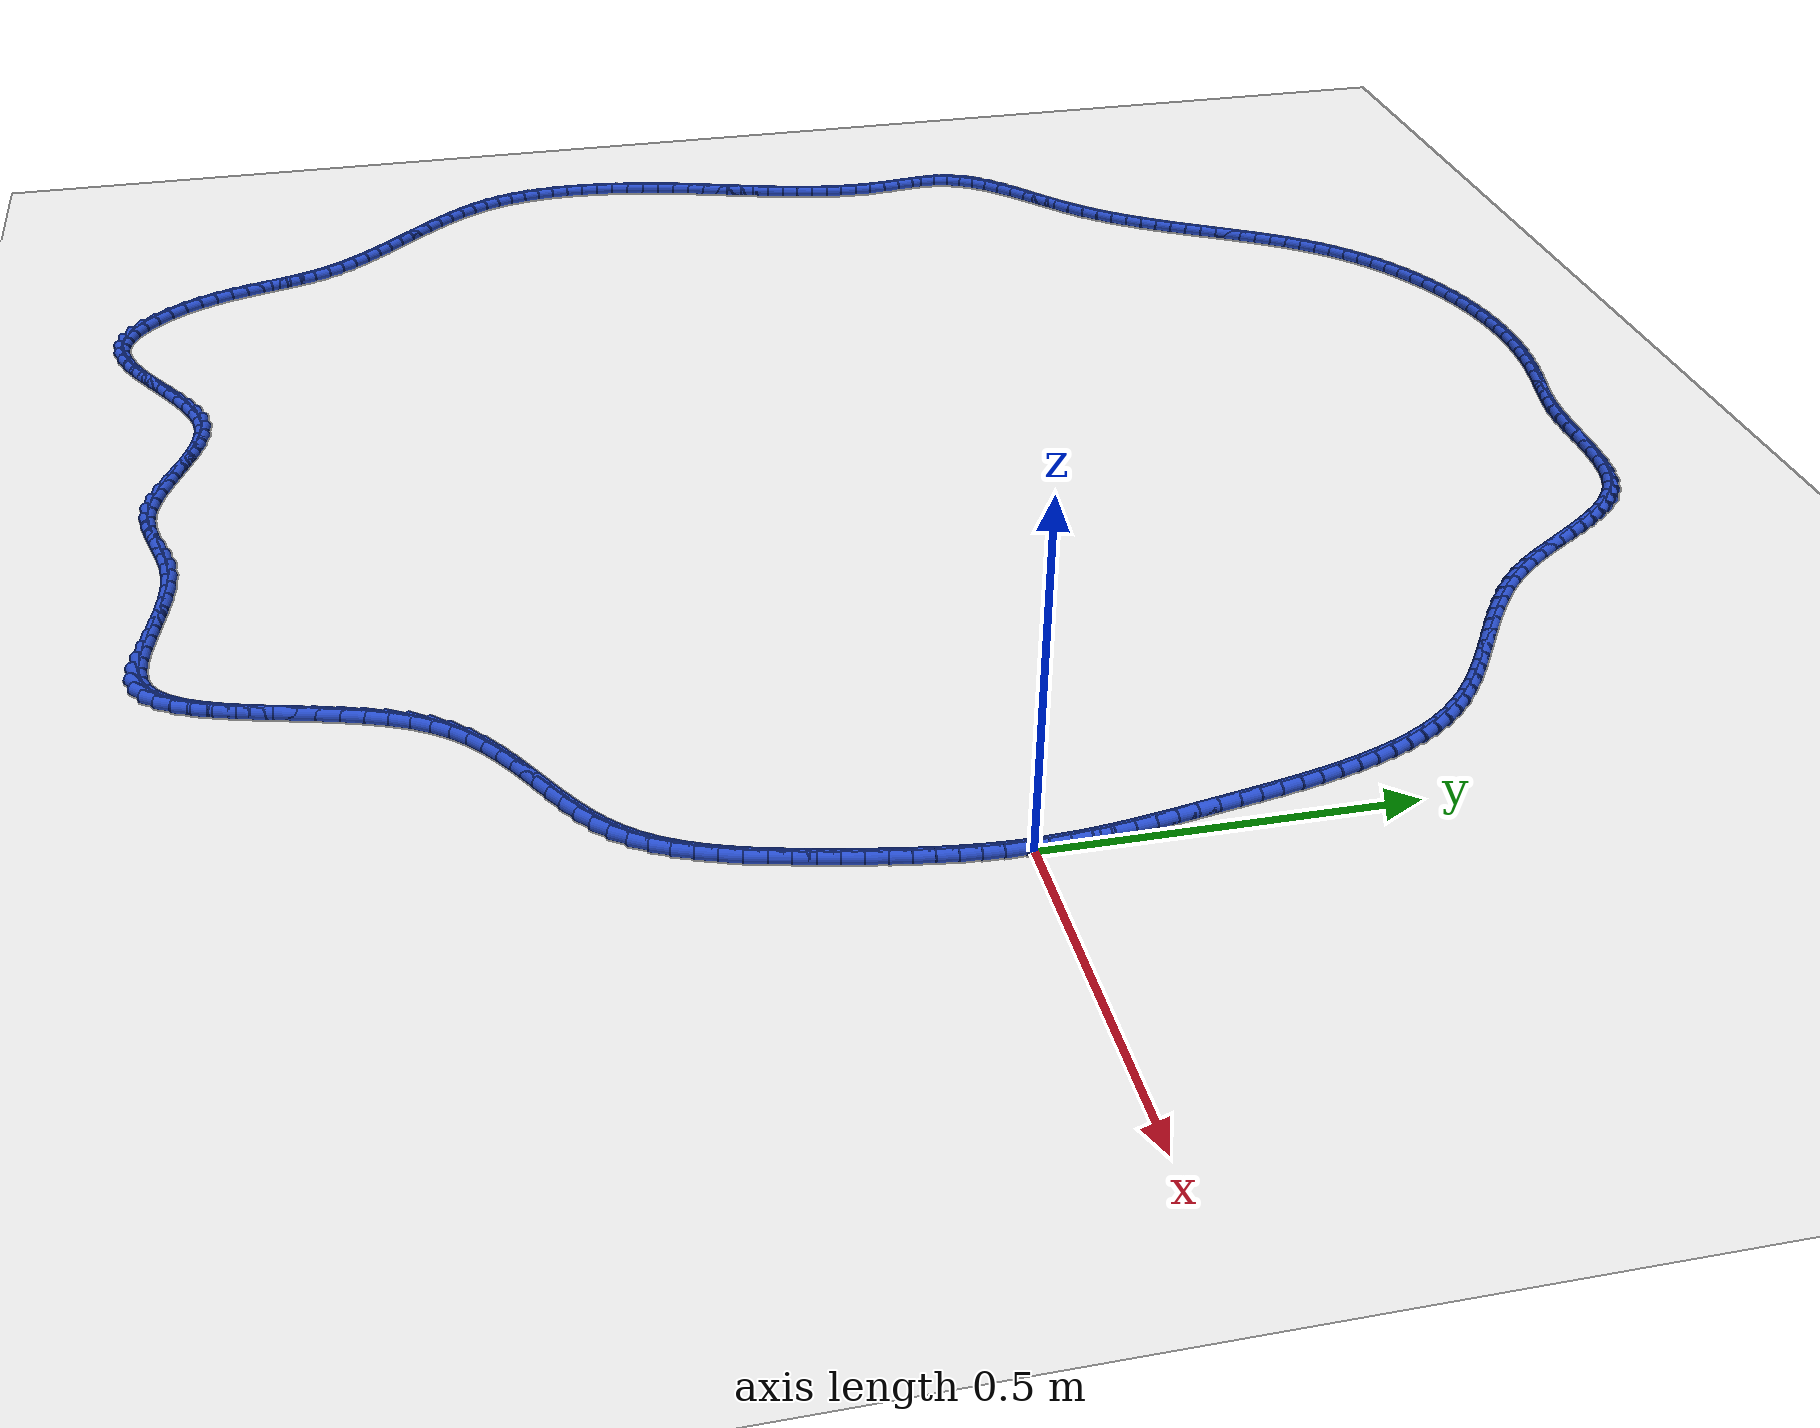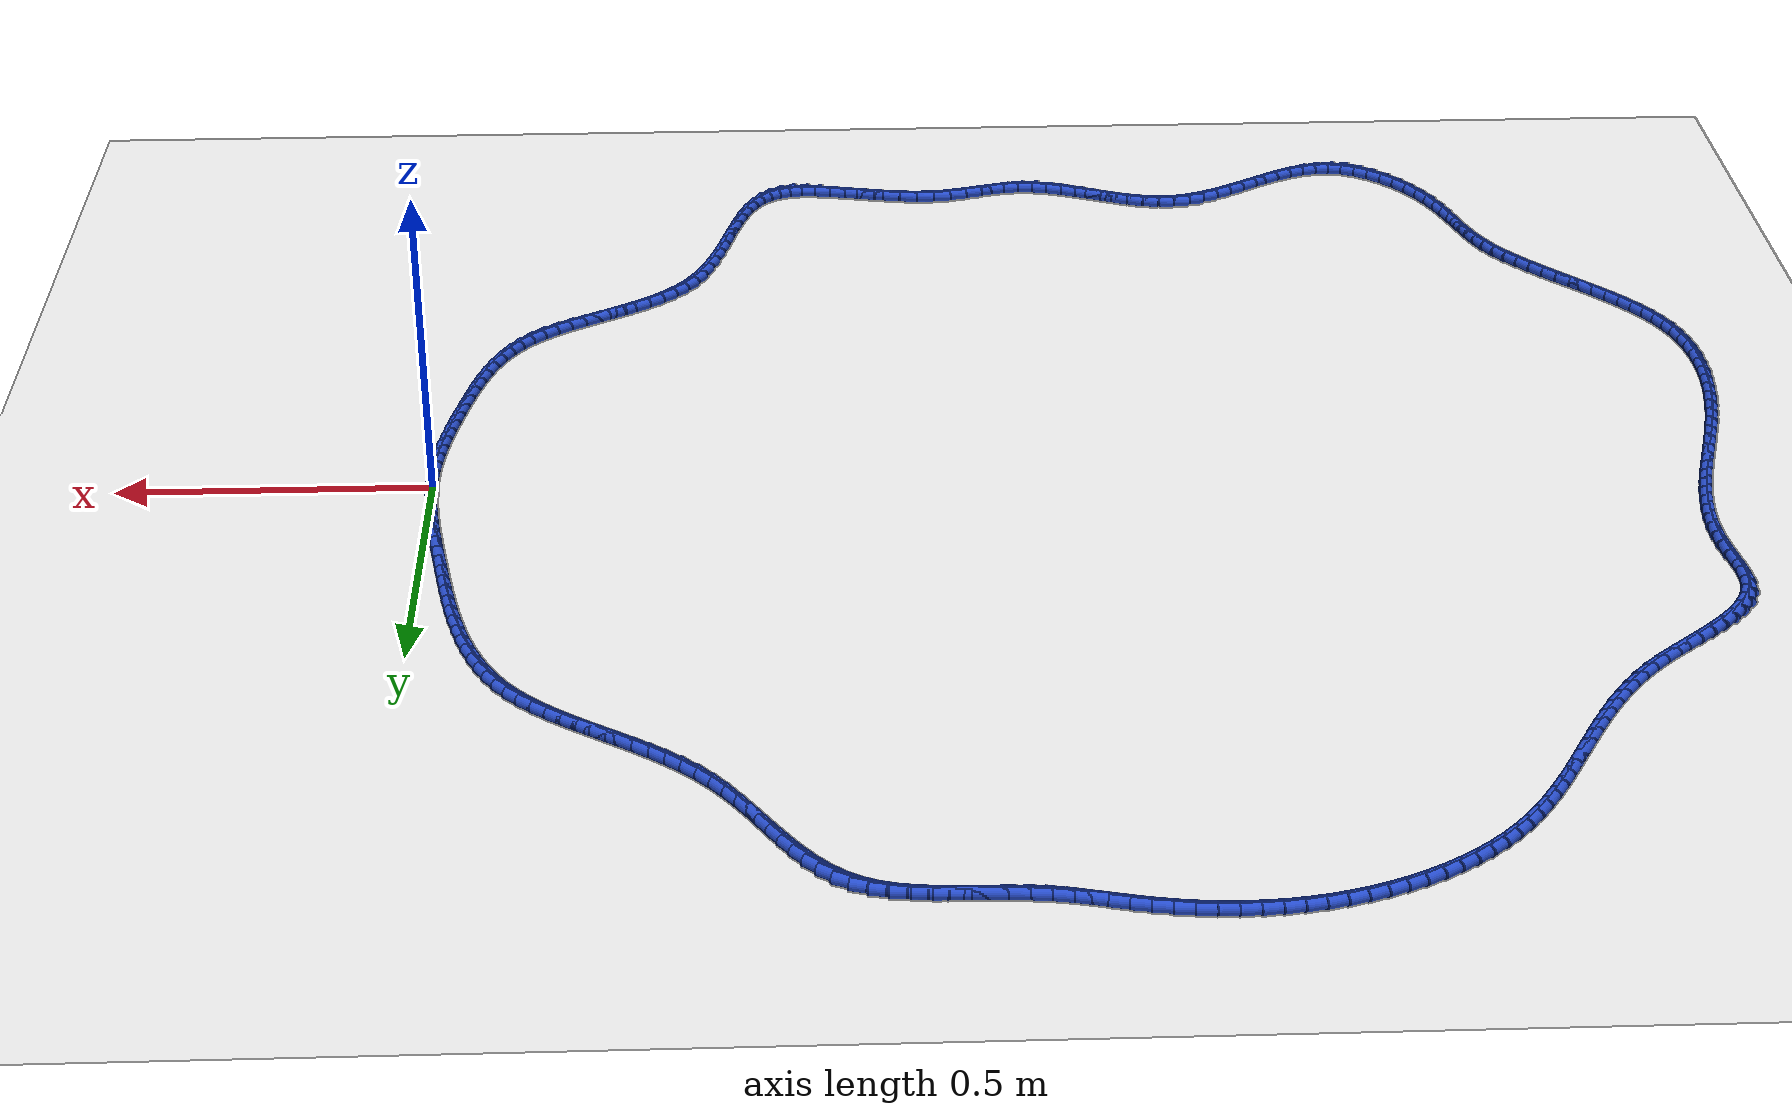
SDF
<sdf version="1.6">
 <world name="default">
  <light name="sun" type="directional">
   <pose>0 0 10 0 -0 0</pose>
   <diffuse>0.8 0.8 0.8 1</diffuse>
   <specular>0.2 0.2 0.2 1</specular>
   <attenuation>
    <range>1000</range>
    <constant>0.9</constant>
    <linear>0.01</linear>
    <quadratic>0.001</quadratic>
   </attenuation>
   <direction>-0.5 0.1 -0.9</direction>
  </light>
  <model name="ground_plane">
   <static>1</static>
   <link name="link">
    <collision name="collision">
     <geometry><plane><normal>0 0 1</normal><size>100 100</size></plane></geometry>
     <surface><friction><ode><mu>100</mu><mu2>50</mu2></ode></friction></surface>
    </collision>
    <visual name="visual">
     <cast_shadows>0</cast_shadows>
     <geometry><plane><normal>0 0 1</normal><size>100 100</size></plane></geometry>
     <material>
      <script><uri>file://media/materials/scripts/gazebo.material</uri><name>Gazebo/WhiteGlow</name></script>
     </material>
    </visual>
   </link>
  </model>
  <gravity>0 0 -9.8</gravity>
  <magnetic_field>6e-06 2.3e-05 -4.2e-05</magnetic_field>
  <atmosphere type="adiabatic"/>
  <physics name="default_physics" default="0" type="ode">
   <max_step_size>0.001</max_step_size>
   <real_time_factor>1</real_time_factor>
   <real_time_update_rate>1000</real_time_update_rate>
  </physics>
  <scene><ambient>0.4 0.4 0.4 1</ambient><background>0.7 0.7 0.7 1</background><shadows>1</shadows></scene>
  <spherical_coordinates>
   <surface_model>EARTH_WGS84</surface_model>
   <latitude_deg>0</latitude_deg>
   <longitude_deg>0</longitude_deg>
   <elevation>0</elevation>
   <heading_deg>0</heading_deg>
  </spherical_coordinates>
  <model name="line">
   <link name="link_0">
    <pose>5.204170427930421e-18 0.0 0.01 0 1.57 -1.54424491713909</pose>
    <collision name="collision">
     <geometry><cylinder><radius>0.01</radius><length>0.08</length></cylinder></geometry>
    </collision>
    <visual name="visual">
     <material>
      <script><name>Gazebo/Blue</name><uri>file://media/materials/scripts/gazebo.material</uri></script>
     </material>
     <geometry><cylinder><radius>0.01</radius><length>0.08</length></cylinder></geometry>
    </visual>
   </link>
   <link name="link_1">
    <pose>-0.0007331389624055258 0.027605565267062034 0.01 0 1.57 -1.5083042285073311</pose>
    <collision name="collision">
     <geometry><cylinder><radius>0.01</radius><length>0.08</length></cylinder></geometry>
    </collision>
    <visual name="visual">
     <material>
      <script><name>Gazebo/Blue</name><uri>file://media/materials/scripts/gazebo.material</uri></script>
     </material>
     <geometry><cylinder><radius>0.01</radius><length>0.08</length></cylinder></geometry>
    </visual>
   </link>
   <link name="link_2">
    <pose>-0.0024619686038296245 0.05523431500493752 0.01 0 1.57 -1.4771421987249218</pose>
    <collision name="collision">
     <geometry><cylinder><radius>0.01</radius><length>0.08</length></cylinder></geometry>
    </collision>
    <visual name="visual">
     <material>
      <script><name>Gazebo/Blue</name><uri>file://media/materials/scripts/gazebo.material</uri></script>
     </material>
     <geometry><cylinder><radius>0.01</radius><length>0.08</length></cylinder></geometry>
    </visual>
   </link>
   <link name="link_3">
    <pose>-0.005062239104522836 0.08291770385107804 0.01 0 1.57 -1.4508305532315364</pose>
    <collision name="collision">
     <geometry><cylinder><radius>0.01</radius><length>0.08</length></cylinder></geometry>
    </collision>
    <visual name="visual">
     <material>
      <script><name>Gazebo/Blue</name><uri>file://media/materials/scripts/gazebo.material</uri></script>
     </material>
     <geometry><cylinder><radius>0.01</radius><length>0.08</length></cylinder></geometry>
    </visual>
   </link>
   <link name="link_4">
    <pose>-0.008409700644735745 0.11068718644293517 0.01 0 1.57 -1.4293722706245764</pose>
    <collision name="collision">
     <geometry><cylinder><radius>0.01</radius><length>0.08</length></cylinder></geometry>
    </collision>
    <visual name="visual">
     <material>
      <script><name>Gazebo/Blue</name><uri>file://media/materials/scripts/gazebo.material</uri></script>
     </material>
     <geometry><cylinder><radius>0.01</radius><length>0.08</length></cylinder></geometry>
    </visual>
   </link>
   <link name="link_5">
    <pose>-0.012380103404718904 0.13857421741796055 0.01 0 1.57 -1.4127209131629384</pose>
    <collision name="collision">
     <geometry><cylinder><radius>0.01</radius><length>0.08</length></cylinder></geometry>
    </collision>
    <visual name="visual">
     <material>
      <script><name>Gazebo/Blue</name><uri>file://media/materials/scripts/gazebo.material</uri></script>
     </material>
     <geometry><cylinder><radius>0.01</radius><length>0.08</length></cylinder></geometry>
    </visual>
   </link>
   <link name="link_6">
    <pose>-0.01684919756472287 0.1666102514136057 0.01 0 1.57 -1.400796930961854</pose>
    <collision name="collision">
     <geometry><cylinder><radius>0.01</radius><length>0.08</length></cylinder></geometry>
    </collision>
    <visual name="visual">
     <material>
      <script><name>Gazebo/Blue</name><uri>file://media/materials/scripts/gazebo.material</uri></script>
     </material>
     <geometry><cylinder><radius>0.01</radius><length>0.08</length></cylinder></geometry>
    </visual>
   </link>
   <link name="link_7">
    <pose>-0.021692733304998206 0.19482674306732223 0.01 0 1.57 -1.3935002870489166</pose>
    <collision name="collision">
     <geometry><cylinder><radius>0.01</radius><length>0.08</length></cylinder></geometry>
    </collision>
    <visual name="visual">
     <material>
      <script><name>Gazebo/Blue</name><uri>file://media/materials/scripts/gazebo.material</uri></script>
     </material>
     <geometry><cylinder><radius>0.01</radius><length>0.08</length></cylinder></geometry>
    </visual>
   </link>
   <link name="link_8">
    <pose>-0.026786460805795477 0.22325514701656177 0.01 0 1.57 -1.3907170963987456</pose>
    <collision name="collision">
     <geometry><cylinder><radius>0.01</radius><length>0.08</length></cylinder></geometry>
    </collision>
    <visual name="visual">
     <material>
      <script><name>Gazebo/Blue</name><uri>file://media/materials/scripts/gazebo.material</uri></script>
     </material>
     <geometry><cylinder><radius>0.01</radius><length>0.08</length></cylinder></geometry>
    </visual>
   </link>
   <link name="link_9">
    <pose>-0.032006189531151204 0.2519268802707705 0.01 0 1.57 -1.3901957982833777</pose>
    <collision name="collision">
     <geometry><cylinder><radius>0.01</radius><length>0.08</length></cylinder></geometry>
    </collision>
    <visual name="visual">
     <material>
      <script><name>Gazebo/Blue</name><uri>file://media/materials/scripts/gazebo.material</uri></script>
     </material>
     <geometry><cylinder><radius>0.01</radius><length>0.08</length></cylinder></geometry>
    </visual>
   </link>
   <link name="link_10">
    <pose>-0.037284901697947806 0.2808370717276328 0.01 0 1.57 -1.38579645625047</pose>
    <collision name="collision">
     <geometry><cylinder><radius>0.01</radius><length>0.08</length></cylinder></geometry>
    </collision>
    <visual name="visual">
     <material>
      <script><name>Gazebo/Blue</name><uri>file://media/materials/scripts/gazebo.material</uri></script>
     </material>
     <geometry><cylinder><radius>0.01</radius><length>0.08</length></cylinder></geometry>
    </visual>
   </link>
   <link name="link_11">
    <pose>-0.042719401227046545 0.30987687102885747 0.01 0 1.57 -1.3764539676866598</pose>
    <collision name="collision">
     <geometry><cylinder><radius>0.01</radius><length>0.08</length></cylinder></geometry>
    </collision>
    <visual name="visual">
     <material>
      <script><name>Gazebo/Blue</name><uri>file://media/materials/scripts/gazebo.material</uri></script>
     </material>
     <geometry><cylinder><radius>0.01</radius><length>0.08</length></cylinder></geometry>
    </visual>
   </link>
   <link name="link_12">
    <pose>-0.04843564924440772 0.3389189214496653 0.01 0 1.57 -1.3621023409759438</pose>
    <collision name="collision">
     <geometry><cylinder><radius>0.01</radius><length>0.08</length></cylinder></geometry>
    </collision>
    <visual name="visual">
     <material>
      <script><name>Gazebo/Blue</name><uri>file://media/materials/scripts/gazebo.material</uri></script>
     </material>
     <geometry><cylinder><radius>0.01</radius><length>0.08</length></cylinder></geometry>
    </visual>
   </link>
   <link name="link_13">
    <pose>-0.054559606875991644 0.36783586626527703 0.01 0 1.57 -1.3425820299071756</pose>
    <collision name="collision">
     <geometry><cylinder><radius>0.01</radius><length>0.08</length></cylinder></geometry>
    </collision>
    <visual name="visual">
     <material>
      <script><name>Gazebo/Blue</name><uri>file://media/materials/scripts/gazebo.material</uri></script>
     </material>
     <geometry><cylinder><radius>0.01</radius><length>0.08</length></cylinder></geometry>
    </visual>
   </link>
   <link name="link_14">
    <pose>-0.06121723524775858 0.3965003487509133 0.01 0 1.57 -1.3176457476866856</pose>
    <collision name="collision">
     <geometry><cylinder><radius>0.01</radius><length>0.08</length></cylinder></geometry>
    </collision>
    <visual name="visual">
     <material>
      <script><name>Gazebo/Blue</name><uri>file://media/materials/scripts/gazebo.material</uri></script>
     </material>
     <geometry><cylinder><radius>0.01</radius><length>0.08</length></cylinder></geometry>
    </visual>
   </link>
   <link name="link_15">
    <pose>-0.06853449548566888 0.42478501218179493 0.01 0 1.57 -1.2869661867693574</pose>
    <collision name="collision">
     <geometry><cylinder><radius>0.01</radius><length>0.08</length></cylinder></geometry>
    </collision>
    <visual name="visual">
     <material>
      <script><name>Gazebo/Blue</name><uri>file://media/materials/scripts/gazebo.material</uri></script>
     </material>
     <geometry><cylinder><radius>0.01</radius><length>0.08</length></cylinder></geometry>
    </visual>
   </link>
   <link name="link_16">
    <pose>-0.07663734871568284 0.45256249983314273 0.01 0 1.57 -1.2501484863901373</pose>
    <collision name="collision">
     <geometry><cylinder><radius>0.01</radius><length>0.08</length></cylinder></geometry>
    </collision>
    <visual name="visual">
     <material>
      <script><name>Gazebo/Blue</name><uri>file://media/materials/scripts/gazebo.material</uri></script>
     </material>
     <geometry><cylinder><radius>0.01</radius><length>0.08</length></cylinder></geometry>
    </visual>
   </link>
   <link name="link_17">
    <pose>-0.08565175606376073 0.47970545498017714 0.01 0 1.57 -1.2067514088748772</pose>
    <collision name="collision">
     <geometry><cylinder><radius>0.01</radius><length>0.08</length></cylinder></geometry>
    </collision>
    <visual name="visual">
     <material>
      <script><name>Gazebo/Blue</name><uri>file://media/materials/scripts/gazebo.material</uri></script>
     </material>
     <geometry><cylinder><radius>0.01</radius><length>0.08</length></cylinder></geometry>
    </visual>
   </link>
   <link name="link_18">
    <pose>-0.0957036786558629 0.5060865208981193 0.01 0 1.57 -1.156322378079311</pose>
    <collision name="collision">
     <geometry><cylinder><radius>0.01</radius><length>0.08</length></cylinder></geometry>
    </collision>
    <visual name="visual">
     <material>
      <script><name>Gazebo/Blue</name><uri>file://media/materials/scripts/gazebo.material</uri></script>
     </material>
     <geometry><cylinder><radius>0.01</radius><length>0.08</length></cylinder></geometry>
    </visual>
   </link>
   <link name="link_19">
    <pose>-0.10691907761794961 0.5315783408621897 0.01 0 1.57 -1.0984522764906532</pose>
    <collision name="collision">
     <geometry><cylinder><radius>0.01</radius><length>0.08</length></cylinder></geometry>
    </collision>
    <visual name="visual">
     <material>
      <script><name>Gazebo/Blue</name><uri>file://media/materials/scripts/gazebo.material</uri></script>
     </material>
     <geometry><cylinder><radius>0.01</radius><length>0.08</length></cylinder></geometry>
    </visual>
   </link>
   <link name="link_20">
    <pose>-0.11942391407598121 0.5560535581476092 0.01 0 1.57 -1.0328550798418064</pose>
    <collision name="collision">
     <geometry><cylinder><radius>0.01</radius><length>0.08</length></cylinder></geometry>
    </collision>
    <visual name="visual">
     <material>
      <script><name>Gazebo/Blue</name><uri>file://media/materials/scripts/gazebo.material</uri></script>
     </material>
     <geometry><cylinder><radius>0.01</radius><length>0.08</length></cylinder></geometry>
    </visual>
   </link>
   <link name="link_21">
    <pose>-0.13334414915591802 0.5793848160295985 0.01 0 1.57 -0.9594732282296928</pose>
    <collision name="collision">
     <geometry><cylinder><radius>0.01</radius><length>0.08</length></cylinder></geometry>
    </collision>
    <visual name="visual">
     <material>
      <script><name>Gazebo/Blue</name><uri>file://media/materials/scripts/gazebo.material</uri></script>
     </material>
     <geometry><cylinder><radius>0.01</radius><length>0.08</length></cylinder></geometry>
    </visual>
   </link>
   <link name="link_22">
    <pose>-0.1488057439837202 0.6014447577833781 0.01 0 1.57 -0.8787318189471565</pose>
    <collision name="collision">
     <geometry><cylinder><radius>0.01</radius><length>0.08</length></cylinder></geometry>
    </collision>
    <visual name="visual">
     <material>
      <script><name>Gazebo/Blue</name><uri>file://media/materials/scripts/gazebo.material</uri></script>
     </material>
     <geometry><cylinder><radius>0.01</radius><length>0.08</length></cylinder></geometry>
    </visual>
   </link>
   <link name="link_23">
    <pose>-0.16593216040267747 0.6221085500558945 0.01 0 1.57 -0.7987148305769167</pose>
    <collision name="collision">
     <geometry><cylinder><radius>0.01</radius><length>0.08</length></cylinder></geometry>
    </collision>
    <visual name="visual">
     <material>
      <script><name>Gazebo/Blue</name><uri>file://media/materials/scripts/gazebo.material</uri></script>
     </material>
     <geometry><cylinder><radius>0.01</radius><length>0.08</length></cylinder></geometry>
    </visual>
   </link>
   <link name="link_24">
    <pose>-0.1847081599979109 0.6413913965990775 0.01 0 1.57 -0.731348205295567</pose>
    <collision name="collision">
     <geometry><cylinder><radius>0.01</radius><length>0.08</length></cylinder></geometry>
    </collision>
    <visual name="visual">
     <material>
      <script><name>Gazebo/Blue</name><uri>file://media/materials/scripts/gazebo.material</uri></script>
     </material>
     <geometry><cylinder><radius>0.01</radius><length>0.08</length></cylinder></geometry>
    </visual>
   </link>
   <link name="link_25">
    <pose>-0.20490975324323477 0.6595192643002379 0.01 0 1.57 -0.6777987573484665</pose>
    <collision name="collision">
     <geometry><cylinder><radius>0.01</radius><length>0.08</length></cylinder></geometry>
    </collision>
    <visual name="visual">
     <material>
      <script><name>Gazebo/Blue</name><uri>file://media/materials/scripts/gazebo.material</uri></script>
     </material>
     <geometry><cylinder><radius>0.01</radius><length>0.08</length></cylinder></geometry>
    </visual>
   </link>
   <link name="link_26">
    <pose>-0.22629570291233347 0.6767355339868307 0.01 0 1.57 -0.6377801426772267</pose>
    <collision name="collision">
     <geometry><cylinder><radius>0.01</radius><length>0.08</length></cylinder></geometry>
    </collision>
    <visual name="visual">
     <material>
      <script><name>Gazebo/Blue</name><uri>file://media/materials/scripts/gazebo.material</uri></script>
     </material>
     <geometry><cylinder><radius>0.01</radius><length>0.08</length></cylinder></geometry>
    </visual>
   </link>
   <link name="link_27">
    <pose>-0.24862477177889136 0.6932835864863115 0.01 0 1.57 -0.6107711473684513</pose>
    <collision name="collision">
     <geometry><cylinder><radius>0.01</radius><length>0.08</length></cylinder></geometry>
    </collision>
    <visual name="visual">
     <material>
      <script><name>Gazebo/Blue</name><uri>file://media/materials/scripts/gazebo.material</uri></script>
     </material>
     <geometry><cylinder><radius>0.01</radius><length>0.08</length></cylinder></geometry>
    </visual>
   </link>
   <link name="link_28">
    <pose>-0.27165572261659326 0.7094068026261356 0.01 0 1.57 -0.5962293091006922</pose>
    <collision name="collision">
     <geometry><cylinder><radius>0.01</radius><length>0.08</length></cylinder></geometry>
    </collision>
    <visual name="visual">
     <material>
      <script><name>Gazebo/Blue</name><uri>file://media/materials/scripts/gazebo.material</uri></script>
     </material>
     <geometry><cylinder><radius>0.01</radius><length>0.08</length></cylinder></geometry>
    </visual>
   </link>
   <link name="link_29">
    <pose>-0.29514731819912343 0.7253485632337584 0.01 0 1.57 -0.5937137042425366</pose>
    <collision name="collision">
     <geometry><cylinder><radius>0.01</radius><length>0.08</length></cylinder></geometry>
    </collision>
    <visual name="visual">
     <material>
      <script><name>Gazebo/Blue</name><uri>file://media/materials/scripts/gazebo.material</uri></script>
     </material>
     <geometry><cylinder><radius>0.01</radius><length>0.08</length></cylinder></geometry>
    </visual>
   </link>
   <link name="link_30">
    <pose>-0.31885832130016634 0.741352249136635 0.01 0 1.57 -0.6029373252482946</pose>
    <collision name="collision">
     <geometry><cylinder><radius>0.01</radius><length>0.08</length></cylinder></geometry>
    </collision>
    <visual name="visual">
     <material>
      <script><name>Gazebo/Blue</name><uri>file://media/materials/scripts/gazebo.material</uri></script>
     </material>
     <geometry><cylinder><radius>0.01</radius><length>0.08</length></cylinder></geometry>
    </visual>
   </link>
   <link name="link_31">
    <pose>-0.3425474946934065 0.757661241162221 0.01 0 1.57 -0.6237666766379742</pose>
    <collision name="collision">
     <geometry><cylinder><radius>0.01</radius><length>0.08</length></cylinder></geometry>
    </collision>
    <visual name="visual">
     <material>
      <script><name>Gazebo/Blue</name><uri>file://media/materials/scripts/gazebo.material</uri></script>
     </material>
     <geometry><cylinder><radius>0.01</radius><length>0.08</length></cylinder></geometry>
    </visual>
   </link>
   <link name="link_32">
    <pose>-0.3659736011525285 0.7745189201379715 0.01 0 1.57 -0.6561775946210243</pose>
    <collision name="collision">
     <geometry><cylinder><radius>0.01</radius><length>0.08</length></cylinder></geometry>
    </collision>
    <visual name="visual">
     <material>
      <script><name>Gazebo/Blue</name><uri>file://media/materials/scripts/gazebo.material</uri></script>
     </material>
     <geometry><cylinder><radius>0.01</radius><length>0.08</length></cylinder></geometry>
    </visual>
   </link>
   <link name="link_33">
    <pose>-0.3888954034512167 0.7921686668913419 0.01 0 1.57 -0.700168496380361</pose>
    <collision name="collision">
     <geometry><cylinder><radius>0.01</radius><length>0.08</length></cylinder></geometry>
    </collision>
    <visual name="visual">
     <material>
      <script><name>Gazebo/Blue</name><uri>file://media/materials/scripts/gazebo.material</uri></script>
     </material>
     <geometry><cylinder><radius>0.01</radius><length>0.08</length></cylinder></geometry>
    </visual>
   </link>
   <link name="link_34">
    <pose>-0.41107166436315556 0.8108538622497875 0.01 0 1.57 -0.7556292426508752</pose>
    <collision name="collision">
     <geometry><cylinder><radius>0.01</radius><length>0.08</length></cylinder></geometry>
    </collision>
    <visual name="visual">
     <material>
      <script><name>Gazebo/Blue</name><uri>file://media/materials/scripts/gazebo.material</uri></script>
     </material>
     <geometry><cylinder><radius>0.01</radius><length>0.08</length></cylinder></geometry>
    </visual>
   </link>
   <link name="link_35">
    <pose>-0.43226114666202964 0.8308178870407636 0.01 0 1.57 -0.8221605860373753</pose>
    <collision name="collision">
     <geometry><cylinder><radius>0.01</radius><length>0.08</length></cylinder></geometry>
    </collision>
    <visual name="visual">
     <material>
      <script><name>Gazebo/Blue</name><uri>file://media/materials/scripts/gazebo.material</uri></script>
     </material>
     <geometry><cylinder><radius>0.01</radius><length>0.08</length></cylinder></geometry>
    </visual>
   </link>
   <link name="link_36">
    <pose>-0.4522227718889885 0.852303915212467 0.01 0 1.57 -0.8919763719669657</pose>
    <collision name="collision">
     <geometry><cylinder><radius>0.01</radius><length>0.08</length></cylinder></geometry>
    </collision>
    <visual name="visual">
     <material>
      <script><name>Gazebo/Blue</name><uri>file://media/materials/scripts/gazebo.material</uri></script>
     </material>
     <geometry><cylinder><radius>0.01</radius><length>0.08</length></cylinder></geometry>
    </visual>
   </link>
   <link name="link_37">
    <pose>-0.4708443272475295 0.8753872044926834 0.01 0 1.57 -0.9455403787608486</pose>
    <collision name="collision">
     <geometry><cylinder><radius>0.01</radius><length>0.08</length></cylinder></geometry>
    </collision>
    <visual name="visual">
     <material>
      <script><name>Gazebo/Blue</name><uri>file://media/materials/scripts/gazebo.material</uri></script>
     </material>
     <geometry><cylinder><radius>0.01</radius><length>0.08</length></cylinder></geometry>
    </visual>
   </link>
   <link name="link_38">
    <pose>-0.4883749751700896 0.8996721287330119 0.01 0 1.57 -0.9806072500335061</pose>
    <collision name="collision">
     <geometry><cylinder><radius>0.01</radius><length>0.08</length></cylinder></geometry>
    </collision>
    <visual name="visual">
     <material>
      <script><name>Gazebo/Blue</name><uri>file://media/materials/scripts/gazebo.material</uri></script>
     </material>
     <geometry><cylinder><radius>0.01</radius><length>0.08</length></cylinder></geometry>
    </visual>
   </link>
   <link name="link_39">
    <pose>-0.505126748722248 0.924681139270552 0.01 0 1.57 -0.9980810034869929</pose>
    <collision name="collision">
     <geometry><cylinder><radius>0.01</radius><length>0.08</length></cylinder></geometry>
    </collision>
    <visual name="visual">
     <material>
      <script><name>Gazebo/Blue</name><uri>file://media/materials/scripts/gazebo.material</uri></script>
     </material>
     <geometry><cylinder><radius>0.01</radius><length>0.08</length></cylinder></geometry>
    </visual>
   </link>
   <link name="link_40">
    <pose>-0.5214116809695839 0.9499366874424021 0.01 0 1.57 -0.9982461652650182</pose>
    <collision name="collision">
     <geometry><cylinder><radius>0.01</radius><length>0.08</length></cylinder></geometry>
    </collision>
    <visual name="visual">
     <material>
      <script><name>Gazebo/Blue</name><uri>file://media/materials/scripts/gazebo.material</uri></script>
     </material>
     <geometry><cylinder><radius>0.01</radius><length>0.08</length></cylinder></geometry>
    </visual>
   </link>
   <link name="link_41">
    <pose>-0.5375418049776769 0.9749612245856625 0.01 0 1.57 -0.9806132313942009</pose>
    <collision name="collision">
     <geometry><cylinder><radius>0.01</radius><length>0.08</length></cylinder></geometry>
    </collision>
    <visual name="visual">
     <material>
      <script><name>Gazebo/Blue</name><uri>file://media/materials/scripts/gazebo.material</uri></script>
     </material>
     <geometry><cylinder><radius>0.01</radius><length>0.08</length></cylinder></geometry>
    </visual>
   </link>
   <link name="link_42">
    <pose>-0.5538291538121063 0.9992772020374322 0.01 0 1.57 -0.9438438299455865</pose>
    <collision name="collision">
     <geometry><cylinder><radius>0.01</radius><length>0.08</length></cylinder></geometry>
    </collision>
    <visual name="visual">
     <material>
      <script><name>Gazebo/Blue</name><uri>file://media/materials/scripts/gazebo.material</uri></script>
     </material>
     <geometry><cylinder><radius>0.01</radius><length>0.08</length></cylinder></geometry>
    </visual>
   </link>
   <link name="link_43">
    <pose>-0.5705857605384517 1.0224070711348103 0.01 0 1.57 -0.8857750793815372</pose>
    <collision name="collision">
     <geometry><cylinder><radius>0.01</radius><length>0.08</length></cylinder></geometry>
    </collision>
    <visual name="visual">
     <material>
      <script><name>Gazebo/Blue</name><uri>file://media/materials/scripts/gazebo.material</uri></script>
     </material>
     <geometry><cylinder><radius>0.01</radius><length>0.08</length></cylinder></geometry>
    </visual>
   </link>
   <link name="link_44">
    <pose>-0.5881236582222917 1.0438732832148963 0.01 0 1.57 -0.8036746749834545</pose>
    <collision name="collision">
     <geometry><cylinder><radius>0.01</radius><length>0.08</length></cylinder></geometry>
    </collision>
    <visual name="visual">
     <material>
      <script><name>Gazebo/Blue</name><uri>file://media/materials/scripts/gazebo.material</uri></script>
     </material>
     <geometry><cylinder><radius>0.01</radius><length>0.08</length></cylinder></geometry>
    </visual>
   </link>
   <link name="link_45">
    <pose>-0.6067548799292067 1.0631982896147896 0.01 0 1.57 -0.6950063408108956</pose>
    <collision name="collision">
     <geometry><cylinder><radius>0.01</radius><length>0.08</length></cylinder></geometry>
    </collision>
    <visual name="visual">
     <material>
      <script><name>Gazebo/Blue</name><uri>file://media/materials/scripts/gazebo.material</uri></script>
     </material>
     <geometry><cylinder><radius>0.01</radius><length>0.08</length></cylinder></geometry>
    </visual>
   </link>
   <link name="link_46">
    <pose>-0.6267914587247754 1.0799045416715896 0.01 0 1.57 -0.5590526653572756</pose>
    <collision name="collision">
     <geometry><cylinder><radius>0.01</radius><length>0.08</length></cylinder></geometry>
    </collision>
    <visual name="visual">
     <material>
      <script><name>Gazebo/Blue</name><uri>file://media/materials/scripts/gazebo.material</uri></script>
     </material>
     <geometry><cylinder><radius>0.01</radius><length>0.08</length></cylinder></geometry>
    </visual>
   </link>
   <link name="link_47">
    <pose>-0.6485454276745776 1.0935144907223955 0.01 0 1.57 -0.4036813446365644</pose>
    <collision name="collision">
     <geometry><cylinder><radius>0.01</radius><length>0.08</length></cylinder></geometry>
    </collision>
    <visual name="visual">
     <material>
      <script><name>Gazebo/Blue</name><uri>file://media/materials/scripts/gazebo.material</uri></script>
     </material>
     <geometry><cylinder><radius>0.01</radius><length>0.08</length></cylinder></geometry>
    </visual>
   </link>
   <link name="link_48">
    <pose>-0.6722720650776802 1.103649072459971 0.01 0 1.57 -0.26707504589939135</pose>
    <collision name="collision">
     <geometry><cylinder><radius>0.01</radius><length>0.08</length></cylinder></geometry>
    </collision>
    <visual name="visual">
     <material>
      <script><name>Gazebo/Blue</name><uri>file://media/materials/scripts/gazebo.material</uri></script>
     </material>
     <geometry><cylinder><radius>0.01</radius><length>0.08</length></cylinder></geometry>
    </visual>
   </link>
   <link name="link_49">
    <pose>-0.697817799447143 1.1106386838296387 0.01 0 1.57 -0.1644508309351958</pose>
    <collision name="collision">
     <geometry><cylinder><radius>0.01</radius><length>0.08</length></cylinder></geometry>
    </collision>
    <visual name="visual">
     <material>
      <script><name>Gazebo/Blue</name><uri>file://media/materials/scripts/gazebo.material</uri></script>
     </material>
     <geometry><cylinder><radius>0.01</radius><length>0.08</length></cylinder></geometry>
    </visual>
   </link>
   <link name="link_50">
    <pose>-0.7248498800536207 1.1151246445999667 0.01 0 1.57 -0.09286532634721671</pose>
    <collision name="collision">
     <geometry><cylinder><radius>0.01</radius><length>0.08</length></cylinder></geometry>
    </collision>
    <visual name="visual">
     <material>
      <script><name>Gazebo/Blue</name><uri>file://media/materials/scripts/gazebo.material</uri></script>
     </material>
     <geometry><cylinder><radius>0.01</radius><length>0.08</length></cylinder></geometry>
    </visual>
   </link>
   <link name="link_51">
    <pose>-0.7530347945979133 1.1177495960622963 0.01 0 1.57 -0.048457828810924454</pose>
    <collision name="collision">
     <geometry><cylinder><radius>0.01</radius><length>0.08</length></cylinder></geometry>
    </collision>
    <visual name="visual">
     <material>
      <script><name>Gazebo/Blue</name><uri>file://media/materials/scripts/gazebo.material</uri></script>
     </material>
     <geometry><cylinder><radius>0.01</radius><length>0.08</length></cylinder></geometry>
    </visual>
   </link>
   <link name="link_52">
    <pose>-0.7820390307808209 1.1191561795079714 0.01 0 1.57 -0.02816669050583795</pose>
    <collision name="collision">
     <geometry><cylinder><radius>0.01</radius><length>0.08</length></cylinder></geometry>
    </collision>
    <visual name="visual">
     <material>
      <script><name>Gazebo/Blue</name><uri>file://media/materials/scripts/gazebo.material</uri></script>
     </material>
     <geometry><cylinder><radius>0.01</radius><length>0.08</length></cylinder></geometry>
    </visual>
   </link>
   <link name="link_53">
    <pose>-0.8115290763031429 1.1199870362283328 0.01 0 1.57 -0.03027753053303978</pose>
    <collision name="collision">
     <geometry><cylinder><radius>0.01</radius><length>0.08</length></cylinder></geometry>
    </collision>
    <visual name="visual">
     <material>
      <script><name>Gazebo/Blue</name><uri>file://media/materials/scripts/gazebo.material</uri></script>
     </material>
     <geometry><cylinder><radius>0.01</radius><length>0.08</length></cylinder></geometry>
    </visual>
   </link>
   <link name="link_54">
    <pose>-0.8411714188656796 1.120884807514723 0.01 0 1.57 -0.05450352317988771</pose>
    <collision name="collision">
     <geometry><cylinder><radius>0.01</radius><length>0.08</length></cylinder></geometry>
    </collision>
    <visual name="visual">
     <material>
      <script><name>Gazebo/Blue</name><uri>file://media/materials/scripts/gazebo.material</uri></script>
     </material>
     <geometry><cylinder><radius>0.01</radius><length>0.08</length></cylinder></geometry>
    </visual>
   </link>
   <link name="link_55">
    <pose>-0.8706325461692309 1.1224921346584849 0.01 0 1.57 -0.10188749627875246</pose>
    <collision name="collision">
     <geometry><cylinder><radius>0.01</radius><length>0.08</length></cylinder></geometry>
    </collision>
    <visual name="visual">
     <material>
      <script><name>Gazebo/Blue</name><uri>file://media/materials/scripts/gazebo.material</uri></script>
     </material>
     <geometry><cylinder><radius>0.01</radius><length>0.08</length></cylinder></geometry>
    </visual>
   </link>
   <link name="link_56">
    <pose>-0.8995789459145963 1.1254516589509596 0.01 0 1.57 -0.1663708680353121</pose>
    <collision name="collision">
     <geometry><cylinder><radius>0.01</radius><length>0.08</length></cylinder></geometry>
    </collision>
    <visual name="visual">
     <material>
      <script><name>Gazebo/Blue</name><uri>file://media/materials/scripts/gazebo.material</uri></script>
     </material>
     <geometry><cylinder><radius>0.01</radius><length>0.08</length></cylinder></geometry>
    </visual>
   </link>
   <link name="link_57">
    <pose>-0.9277752233743414 1.1301864642435089 0.01 0 1.57 -0.21522411623565835</pose>
    <collision name="collision">
     <geometry><cylinder><radius>0.01</radius><length>0.08</length></cylinder></geometry>
    </collision>
    <visual name="visual">
     <material>
      <script><name>Gazebo/Blue</name><uri>file://media/materials/scripts/gazebo.material</uri></script>
     </material>
     <geometry><cylinder><radius>0.01</radius><length>0.08</length></cylinder></geometry>
    </visual>
   </link>
   <link name="link_58">
    <pose>-0.9553868395924993 1.1362226404505071 0.01 0 1.57 -0.23844774797125545</pose>
    <collision name="collision">
     <geometry><cylinder><radius>0.01</radius><length>0.08</length></cylinder></geometry>
    </collision>
    <visual name="visual">
     <material>
      <script><name>Gazebo/Blue</name><uri>file://media/materials/scripts/gazebo.material</uri></script>
     </material>
     <geometry><cylinder><radius>0.01</radius><length>0.08</length></cylinder></geometry>
    </visual>
   </link>
   <link name="link_59">
    <pose>-0.982681610524131 1.1428572381630924 0.01 0 1.57 -0.235235805202622</pose>
    <collision name="collision">
     <geometry><cylinder><radius>0.01</radius><length>0.08</length></cylinder></geometry>
    </collision>
    <visual name="visual">
     <material>
      <script><name>Gazebo/Blue</name><uri>file://media/materials/scripts/gazebo.material</uri></script>
     </material>
     <geometry><cylinder><radius>0.01</radius><length>0.08</length></cylinder></geometry>
    </visual>
   </link>
   <link name="link_60">
    <pose>-1.0099273521593675 1.149387307893929 0.01 0 1.57 -0.20583534306553503</pose>
    <collision name="collision">
     <geometry><cylinder><radius>0.01</radius><length>0.08</length></cylinder></geometry>
    </collision>
    <visual name="visual">
     <material>
      <script><name>Gazebo/Blue</name><uri>file://media/materials/scripts/gazebo.material</uri></script>
     </material>
     <geometry><cylinder><radius>0.01</radius><length>0.08</length></cylinder></geometry>
    </visual>
   </link>
   <link name="link_61">
    <pose>-1.037386442582831 1.1551205579590513 0.01 0 1.57 -0.16207082154759567</pose>
    <collision name="collision">
     <geometry><cylinder><radius>0.01</radius><length>0.08</length></cylinder></geometry>
    </collision>
    <visual name="visual">
     <material>
      <script><name>Gazebo/Blue</name><uri>file://media/materials/scripts/gazebo.material</uri></script>
     </material>
     <geometry><cylinder><radius>0.01</radius><length>0.08</length></cylinder></geometry>
    </visual>
   </link>
   <link name="link_62">
    <pose>-1.0651689855441946 1.1596631406099343 0.01 0 1.57 -0.11675300569734133</pose>
    <collision name="collision">
     <geometry><cylinder><radius>0.01</radius><length>0.08</length></cylinder></geometry>
    </collision>
    <visual name="visual">
     <material>
      <script><name>Gazebo/Blue</name><uri>file://media/materials/scripts/gazebo.material</uri></script>
     </material>
     <geometry><cylinder><radius>0.01</radius><length>0.08</length></cylinder></geometry>
    </visual>
   </link>
   <link name="link_63">
    <pose>-1.0932159637631305 1.162952670033354 0.01 0 1.57 -0.07039067651279929</pose>
    <collision name="collision">
     <geometry><cylinder><radius>0.01</radius><length>0.08</length></cylinder></geometry>
    </collision>
    <visual name="visual">
     <material>
      <script><name>Gazebo/Blue</name><uri>file://media/materials/scripts/gazebo.material</uri></script>
     </material>
     <geometry><cylinder><radius>0.01</radius><length>0.08</length></cylinder></geometry>
    </visual>
   </link>
   <link name="link_64">
    <pose>-1.121459541081039 1.1649440446205361 0.01 0 1.57 -0.022839337135392157</pose>
    <collision name="collision">
     <geometry><cylinder><radius>0.01</radius><length>0.08</length></cylinder></geometry>
    </collision>
    <visual name="visual">
     <material>
      <script><name>Gazebo/Blue</name><uri>file://media/materials/scripts/gazebo.material</uri></script>
     </material>
     <geometry><cylinder><radius>0.01</radius><length>0.08</length></cylinder></geometry>
    </visual>
   </link>
   <link name="link_65">
    <pose>-1.1498318813393202 1.165592162762706 0.01 0 1.57 0.026028410227044985</pose>
    <collision name="collision">
     <geometry><cylinder><radius>0.01</radius><length>0.08</length></cylinder></geometry>
    </collision>
    <visual name="visual">
     <material>
      <script><name>Gazebo/Blue</name><uri>file://media/materials/scripts/gazebo.material</uri></script>
     </material>
     <geometry><cylinder><radius>0.01</radius><length>0.08</length></cylinder></geometry>
    </visual>
   </link>
   <link name="link_66">
    <pose>-1.1782651483793742 1.1648519228510892 0.01 0 1.57 0.0763192257150106</pose>
    <collision name="collision">
     <geometry><cylinder><radius>0.01</radius><length>0.08</length></cylinder></geometry>
    </collision>
    <visual name="visual">
     <material>
      <script><name>Gazebo/Blue</name><uri>file://media/materials/scripts/gazebo.material</uri></script>
     </material>
     <geometry><cylinder><radius>0.01</radius><length>0.08</length></cylinder></geometry>
    </visual>
   </link>
   <link name="link_67">
    <pose>-1.2066915060426018 1.1626782232769115 0.01 0 1.57 0.1281146541923208</pose>
    <collision name="collision">
     <geometry><cylinder><radius>0.01</radius><length>0.08</length></cylinder></geometry>
    </collision>
    <visual name="visual">
     <material>
      <script><name>Gazebo/Blue</name><uri>file://media/materials/scripts/gazebo.material</uri></script>
     </material>
     <geometry><cylinder><radius>0.01</radius><length>0.08</length></cylinder></geometry>
    </visual>
   </link>
   <link name="link_68">
    <pose>-1.2350431181704031 1.159025962431399 0.01 0 1.57 0.181339918541836</pose>
    <collision name="collision">
     <geometry><cylinder><radius>0.01</radius><length>0.08</length></cylinder></geometry>
    </collision>
    <visual name="visual">
     <material>
      <script><name>Gazebo/Blue</name><uri>file://media/materials/scripts/gazebo.material</uri></script>
     </material>
     <geometry><cylinder><radius>0.01</radius><length>0.08</length></cylinder></geometry>
    </visual>
   </link>
   <link name="link_69">
    <pose>-1.263250649568294 1.1538539943580917 0.01 0 1.57 0.23459493288735364</pose>
    <collision name="collision">
     <geometry><cylinder><radius>0.01</radius><length>0.08</length></cylinder></geometry>
    </collision>
    <visual name="visual">
     <material>
      <script><name>Gazebo/Blue</name><uri>file://media/materials/scripts/gazebo.material</uri></script>
     </material>
     <geometry><cylinder><radius>0.01</radius><length>0.08</length></cylinder></geometry>
    </visual>
   </link>
   <link name="link_70">
    <pose>-1.2912271157517572 1.1471677460049856 0.01 0 1.57 0.2871604845200584</pose>
    <collision name="collision">
     <geometry><cylinder><radius>0.01</radius><length>0.08</length></cylinder></geometry>
    </collision>
    <visual name="visual">
     <material>
      <script><name>Gazebo/Blue</name><uri>file://media/materials/scripts/gazebo.material</uri></script>
     </material>
     <geometry><cylinder><radius>0.01</radius><length>0.08</length></cylinder></geometry>
    </visual>
   </link>
   <link name="link_71">
    <pose>-1.3188740388072377 1.1390029731532172 0.01 0 1.57 0.33930637816420045</pose>
    <collision name="collision">
     <geometry><cylinder><radius>0.01</radius><length>0.08</length></cylinder></geometry>
    </collision>
    <visual name="visual">
     <material>
      <script><name>Gazebo/Blue</name><uri>file://media/materials/scripts/gazebo.material</uri></script>
     </material>
     <geometry><cylinder><radius>0.01</radius><length>0.08</length></cylinder></geometry>
    </visual>
   </link>
   <link name="link_72">
    <pose>-1.3460927444085493 1.129395949877103 0.01 0 1.57 0.39131966595996676</pose>
    <collision name="collision">
     <geometry><cylinder><radius>0.01</radius><length>0.08</length></cylinder></geometry>
    </collision>
    <visual name="visual">
     <material>
      <script><name>Gazebo/Blue</name><uri>file://media/materials/scripts/gazebo.material</uri></script>
     </material>
     <geometry><cylinder><radius>0.01</radius><length>0.08</length></cylinder></geometry>
    </visual>
   </link>
   <link name="link_73">
    <pose>-1.3727845582295044 1.1183829502509606 0.01 0 1.57 0.4434869690823588</pose>
    <collision name="collision">
     <geometry><cylinder><radius>0.01</radius><length>0.08</length></cylinder></geometry>
    </collision>
    <visual name="visual">
     <material>
      <script><name>Gazebo/Blue</name><uri>file://media/materials/scripts/gazebo.material</uri></script>
     </material>
     <geometry><cylinder><radius>0.01</radius><length>0.08</length></cylinder></geometry>
    </visual>
   </link>
   <link name="link_74">
    <pose>-1.3988508059439173 1.1060002483491063 0.01 0 1.57 0.4960934892066461</pose>
    <collision name="collision">
     <geometry><cylinder><radius>0.01</radius><length>0.08</length></cylinder></geometry>
    </collision>
    <visual name="visual">
     <material>
      <script><name>Gazebo/Blue</name><uri>file://media/materials/scripts/gazebo.material</uri></script>
     </material>
     <geometry><cylinder><radius>0.01</radius><length>0.08</length></cylinder></geometry>
    </visual>
   </link>
   <link name="link_75">
    <pose>-1.424192813225602 1.0922841182458578 0.01 0 1.57 0.5494217967895387</pose>
    <collision name="collision">
     <geometry><cylinder><radius>0.01</radius><length>0.08</length></cylinder></geometry>
    </collision>
    <visual name="visual">
     <material>
      <script><name>Gazebo/Blue</name><uri>file://media/materials/scripts/gazebo.material</uri></script>
     </material>
     <geometry><cylinder><radius>0.01</radius><length>0.08</length></cylinder></geometry>
    </visual>
   </link>
   <link name="link_76">
    <pose>-1.4487119057483715 1.0772708340155328 0.01 0 1.57 0.6037500220967859</pose>
    <collision name="collision">
     <geometry><cylinder><radius>0.01</radius><length>0.08</length></cylinder></geometry>
    </collision>
    <visual name="visual">
     <material>
      <script><name>Gazebo/Blue</name><uri>file://media/materials/scripts/gazebo.material</uri></script>
     </material>
     <geometry><cylinder><radius>0.01</radius><length>0.08</length></cylinder></geometry>
    </visual>
   </link>
   <link name="link_77">
    <pose>-1.4723094091860398 1.0609966697324478 0.01 0 1.57 0.6593490635842197</pose>
    <collision name="collision">
     <geometry><cylinder><radius>0.01</radius><length>0.08</length></cylinder></geometry>
    </collision>
    <visual name="visual">
     <material>
      <script><name>Gazebo/Blue</name><uri>file://media/materials/scripts/gazebo.material</uri></script>
     </material>
     <geometry><cylinder><radius>0.01</radius><length>0.08</length></cylinder></geometry>
    </visual>
   </link>
   <link name="link_78">
    <pose>-1.4948866492124202 1.04349789947092 0.01 0 1.57 0.7164784177701606</pose>
    <collision name="collision">
     <geometry><cylinder><radius>0.01</radius><length>0.08</length></cylinder></geometry>
    </collision>
    <visual name="visual">
     <material>
      <script><name>Gazebo/Blue</name><uri>file://media/materials/scripts/gazebo.material</uri></script>
     </material>
     <geometry><cylinder><radius>0.01</radius><length>0.08</length></cylinder></geometry>
    </visual>
   </link>
   <link name="link_79">
    <pose>-1.5163449515013265 1.0248107973052667 0.01 0 1.57 0.7753802417953028</pose>
    <collision name="collision">
     <geometry><cylinder><radius>0.01</radius><length>0.08</length></cylinder></geometry>
    </collision>
    <visual name="visual">
     <material>
      <script><name>Gazebo/Blue</name><uri>file://media/materials/scripts/gazebo.material</uri></script>
     </material>
     <geometry><cylinder><radius>0.01</radius><length>0.08</length></cylinder></geometry>
    </visual>
   </link>
   <link name="link_80">
    <pose>-1.5365856417265724 1.0049716373098052 0.01 0 1.57 0.8357814736558612</pose>
    <collision name="collision">
     <geometry><cylinder><radius>0.01</radius><length>0.08</length></cylinder></geometry>
    </collision>
    <visual name="visual">
     <material>
      <script><name>Gazebo/Blue</name><uri>file://media/materials/scripts/gazebo.material</uri></script>
     </material>
     <geometry><cylinder><radius>0.01</radius><length>0.08</length></cylinder></geometry>
    </visual>
   </link>
   <link name="link_81">
    <pose>-1.5555233434190827 0.9840226078759673 0.01 0 1.57 0.8920228859091139</pose>
    <collision name="collision">
     <geometry><cylinder><radius>0.01</radius><length>0.08</length></cylinder></geometry>
    </collision>
    <visual name="visual">
     <material>
      <script><name>Gazebo/Blue</name><uri>file://media/materials/scripts/gazebo.material</uri></script>
     </material>
     <geometry><cylinder><radius>0.01</radius><length>0.08</length></cylinder></geometry>
    </visual>
   </link>
   <link name="link_82">
    <pose>-1.5732273117717295 0.9620746709334382 0.01 0 1.57 0.9401763185733379</pose>
    <collision name="collision">
     <geometry><cylinder><radius>0.01</radius><length>0.08</length></cylinder></geometry>
    </collision>
    <visual name="visual">
     <material>
      <script><name>Gazebo/Blue</name><uri>file://media/materials/scripts/gazebo.material</uri></script>
     </material>
     <geometry><cylinder><radius>0.01</radius><length>0.08</length></cylinder></geometry>
    </visual>
   </link>
   <link name="link_83">
    <pose>-1.5898665852714977 0.9392831677460476 0.01 0 1.57 0.9800676047944356</pose>
    <collision name="collision">
     <geometry><cylinder><radius>0.01</radius><length>0.08</length></cylinder></geometry>
    </collision>
    <visual name="visual">
     <material>
      <script><name>Gazebo/Blue</name><uri>file://media/materials/scripts/gazebo.material</uri></script>
     </material>
     <geometry><cylinder><radius>0.01</radius><length>0.08</length></cylinder></geometry>
    </visual>
   </link>
   <link name="link_84">
    <pose>-1.6056118664009287 0.9158041796515557 0.01 0 1.57 1.011733033863947</pose>
    <collision name="collision">
     <geometry><cylinder><radius>0.01</radius><length>0.08</length></cylinder></geometry>
    </collision>
    <visual name="visual">
     <material>
      <script><name>Gazebo/Blue</name><uri>file://media/materials/scripts/gazebo.material</uri></script>
     </material>
     <geometry><cylinder><radius>0.01</radius><length>0.08</length></cylinder></geometry>
    </visual>
   </link>
   <link name="link_85">
    <pose>-1.6206338576425652 0.8917937879877248 0.01 0 1.57 1.0352766196394807</pose>
    <collision name="collision">
     <geometry><cylinder><radius>0.01</radius><length>0.08</length></cylinder></geometry>
    </collision>
    <visual name="visual">
     <material>
      <script><name>Gazebo/Blue</name><uri>file://media/materials/scripts/gazebo.material</uri></script>
     </material>
     <geometry><cylinder><radius>0.01</radius><length>0.08</length></cylinder></geometry>
    </visual>
   </link>
   <link name="link_86">
    <pose>-1.6351032614789498 0.8674080740923159 0.01 0 1.57 1.050806704023197</pose>
    <collision name="collision">
     <geometry><cylinder><radius>0.01</radius><length>0.08</length></cylinder></geometry>
    </collision>
    <visual name="visual">
     <material>
      <script><name>Gazebo/Blue</name><uri>file://media/materials/scripts/gazebo.material</uri></script>
     </material>
     <geometry><cylinder><radius>0.01</radius><length>0.08</length></cylinder></geometry>
    </visual>
   </link>
   <link name="link_87">
    <pose>-1.6491907803926247 0.8428031193030905 0.01 0 1.57 1.0583907871140403</pose>
    <collision name="collision">
     <geometry><cylinder><radius>0.01</radius><length>0.08</length></cylinder></geometry>
    </collision>
    <visual name="visual">
     <material>
      <script><name>Gazebo/Blue</name><uri>file://media/materials/scripts/gazebo.material</uri></script>
     </material>
     <geometry><cylinder><radius>0.01</radius><length>0.08</length></cylinder></geometry>
    </visual>
   </link>
   <link name="link_88">
    <pose>-1.6630671168661324 0.8181350049578103 0.01 0 1.57 1.0580264118566227</pose>
    <collision name="collision">
     <geometry><cylinder><radius>0.01</radius><length>0.08</length></cylinder></geometry>
    </collision>
    <visual name="visual">
     <material>
      <script><name>Gazebo/Blue</name><uri>file://media/materials/scripts/gazebo.material</uri></script>
     </material>
     <geometry><cylinder><radius>0.01</radius><length>0.08</length></cylinder></geometry>
    </visual>
   </link>
   <link name="link_89">
    <pose>-1.676902973382016 0.7935598123942367 0.01 0 1.57 1.0498595523229968</pose>
    <collision name="collision">
     <geometry><cylinder><radius>0.01</radius><length>0.08</length></cylinder></geometry>
    </collision>
    <visual name="visual">
     <material>
      <script><name>Gazebo/Blue</name><uri>file://media/materials/scripts/gazebo.material</uri></script>
     </material>
     <geometry><cylinder><radius>0.01</radius><length>0.08</length></cylinder></geometry>
    </visual>
   </link>
   <link name="link_90">
    <pose>-1.6908685958207024 0.7692212495880354 0.01 0 1.57 1.0352005071771602</pose>
    <collision name="collision">
     <geometry><cylinder><radius>0.01</radius><length>0.08</length></cylinder></geometry>
    </collision>
    <visual name="visual">
     <material>
      <script><name>Gazebo/Blue</name><uri>file://media/materials/scripts/gazebo.material</uri></script>
     </material>
     <geometry><cylinder><radius>0.01</radius><length>0.08</length></cylinder></geometry>
    </visual>
   </link>
   <link name="link_91">
    <pose>-1.7051314541758147 0.7451878013579961 0.01 0 1.57 1.0145852354544191</pose>
    <collision name="collision">
     <geometry><cylinder><radius>0.01</radius><length>0.08</length></cylinder></geometry>
    </collision>
    <visual name="visual">
     <material>
      <script><name>Gazebo/Blue</name><uri>file://media/materials/scripts/gazebo.material</uri></script>
     </material>
     <geometry><cylinder><radius>0.01</radius><length>0.08</length></cylinder></geometry>
    </visual>
   </link>
   <link name="link_92">
    <pose>-1.7198579751731382 0.7214996812330824 0.01 0 1.57 0.98811495338782</pose>
    <collision name="collision">
     <geometry><cylinder><radius>0.01</radius><length>0.08</length></cylinder></geometry>
    </collision>
    <visual name="visual">
     <material>
      <script><name>Gazebo/Blue</name><uri>file://media/materials/scripts/gazebo.material</uri></script>
     </material>
     <geometry><cylinder><radius>0.01</radius><length>0.08</length></cylinder></geometry>
    </visual>
   </link>
   <link name="link_93">
    <pose>-1.7352145836638337 0.6981970519422334 0.01 0 1.57 0.9559972169940716</pose>
    <collision name="collision">
     <geometry><cylinder><radius>0.01</radius><length>0.08</length></cylinder></geometry>
    </collision>
    <visual name="visual">
     <material>
      <script><name>Gazebo/Blue</name><uri>file://media/materials/scripts/gazebo.material</uri></script>
     </material>
     <geometry><cylinder><radius>0.01</radius><length>0.08</length></cylinder></geometry>
    </visual>
   </link>
   <link name="link_94">
    <pose>-1.7513677044990623 0.6753200762143878 0.01 0 1.57 0.918566244228401</pose>
    <collision name="collision">
     <geometry><cylinder><radius>0.01</radius><length>0.08</length></cylinder></geometry>
    </collision>
    <visual name="visual">
     <material>
      <script><name>Gazebo/Blue</name><uri>file://media/materials/scripts/gazebo.material</uri></script>
     </material>
     <geometry><cylinder><radius>0.01</radius><length>0.08</length></cylinder></geometry>
    </visual>
   </link>
   <link name="link_95">
    <pose>-1.7684837625299843 0.6529089167784847 0.01 0 1.57 0.8762977974906834</pose>
    <collision name="collision">
     <geometry><cylinder><radius>0.01</radius><length>0.08</length></cylinder></geometry>
    </collision>
    <visual name="visual">
     <material>
      <script><name>Gazebo/Blue</name><uri>file://media/materials/scripts/gazebo.material</uri></script>
     </material>
     <geometry><cylinder><radius>0.01</radius><length>0.08</length></cylinder></geometry>
    </visual>
   </link>
   <link name="link_96">
    <pose>-1.78672918260776 0.6310037363634627 0.01 0 1.57 0.8298144277699098</pose>
    <collision name="collision">
     <geometry><cylinder><radius>0.01</radius><length>0.08</length></cylinder></geometry>
    </collision>
    <visual name="visual">
     <material>
      <script><name>Gazebo/Blue</name><uri>file://media/materials/scripts/gazebo.material</uri></script>
     </material>
     <geometry><cylinder><radius>0.01</radius><length>0.08</length></cylinder></geometry>
    </visual>
   </link>
   <link name="link_97">
    <pose>-1.8062703895835523 0.6096446976982609 0.01 0 1.57 0.7798954212455946</pose>
    <collision name="collision">
     <geometry><cylinder><radius>0.01</radius><length>0.08</length></cylinder></geometry>
    </collision>
    <visual name="visual">
     <material>
      <script><name>Gazebo/Blue</name><uri>file://media/materials/scripts/gazebo.material</uri></script>
     </material>
     <geometry><cylinder><radius>0.01</radius><length>0.08</length></cylinder></geometry>
    </visual>
   </link>
   <link name="link_98">
    <pose>-1.8272732051176583 0.5888717656516013 0.01 0 1.57 0.7341722182087266</pose>
    <collision name="collision">
     <geometry><cylinder><radius>0.01</radius><length>0.08</length></cylinder></geometry>
    </collision>
    <visual name="visual">
     <material>
      <script><name>Gazebo/Blue</name><uri>file://media/materials/scripts/gazebo.material</uri></script>
     </material>
     <geometry><cylinder><radius>0.01</radius><length>0.08</length></cylinder></geometry>
    </visual>
   </link>
   <link name="link_99">
    <pose>-1.8496791345937955 0.5686513242906687 0.01 0 1.57 0.7087884484067445</pose>
    <collision name="collision">
     <geometry><cylinder><radius>0.01</radius><length>0.08</length></cylinder></geometry>
    </collision>
    <visual name="visual">
     <material>
      <script><name>Gazebo/Blue</name><uri>file://media/materials/scripts/gazebo.material</uri></script>
     </material>
     <geometry><cylinder><radius>0.01</radius><length>0.08</length></cylinder></geometry>
    </visual>
   </link>
   <link name="link_100">
    <pose>-1.8728706290074517 0.5487663752254511 0.01 0 1.57 0.7047873605136897</pose>
    <collision name="collision">
     <geometry><cylinder><radius>0.01</radius><length>0.08</length></cylinder></geometry>
    </collision>
    <visual name="visual">
     <material>
      <script><name>Gazebo/Blue</name><uri>file://media/materials/scripts/gazebo.material</uri></script>
     </material>
     <geometry><cylinder><radius>0.01</radius><length>0.08</length></cylinder></geometry>
    </visual>
   </link>
   <link name="link_101">
    <pose>-1.896144496180895 0.5289718271721537 0.01 0 1.57 0.7220168724286427</pose>
    <collision name="collision">
     <geometry><cylinder><radius>0.01</radius><length>0.08</length></cylinder></geometry>
    </collision>
    <visual name="visual">
     <material>
      <script><name>Gazebo/Blue</name><uri>file://media/materials/scripts/gazebo.material</uri></script>
     </material>
     <geometry><cylinder><radius>0.01</radius><length>0.08</length></cylinder></geometry>
    </visual>
   </link>
   <link name="link_102">
    <pose>-1.9187975439363938 0.5090225888469819 0.01 0 1.57 0.7618885323626686</pose>
    <collision name="collision">
     <geometry><cylinder><radius>0.01</radius><length>0.08</length></cylinder></geometry>
    </collision>
    <visual name="visual">
     <material>
      <script><name>Gazebo/Blue</name><uri>file://media/materials/scripts/gazebo.material</uri></script>
     </material>
     <geometry><cylinder><radius>0.01</radius><length>0.08</length></cylinder></geometry>
    </visual>
   </link>
   <link name="link_103">
    <pose>-1.9401265800962153 0.488673568966141 0.01 0 1.57 0.8273645722936976</pose>
    <collision name="collision">
     <geometry><cylinder><radius>0.01</radius><length>0.08</length></cylinder></geometry>
    </collision>
    <visual name="visual">
     <material>
      <script><name>Gazebo/Blue</name><uri>file://media/materials/scripts/gazebo.material</uri></script>
     </material>
     <geometry><cylinder><radius>0.01</radius><length>0.08</length></cylinder></geometry>
    </visual>
   </link>
   <link name="link_104">
    <pose>-1.9594284124826273 0.4676796762458361 0.01 0 1.57 0.9226746576085141</pose>
    <collision name="collision">
     <geometry><cylinder><radius>0.01</radius><length>0.08</length></cylinder></geometry>
    </collision>
    <visual name="visual">
     <material>
      <script><name>Gazebo/Blue</name><uri>file://media/materials/scripts/gazebo.material</uri></script>
     </material>
     <geometry><cylinder><radius>0.01</radius><length>0.08</length></cylinder></geometry>
    </visual>
   </link>
   <link name="link_105">
    <pose>-1.975999848917899 0.4457958194022733 0.01 0 1.57 1.0521683185473627</pose>
    <collision name="collision">
     <geometry><cylinder><radius>0.01</radius><length>0.08</length></cylinder></geometry>
    </collision>
    <visual name="visual">
     <material>
      <script><name>Gazebo/Blue</name><uri>file://media/materials/scripts/gazebo.material</uri></script>
     </material>
     <geometry><cylinder><radius>0.01</radius><length>0.08</length></cylinder></geometry>
    </visual>
   </link>
   <link name="link_106">
    <pose>-1.9891376972242967 0.42277690715165667 0.01 0 1.57 1.2173750922639242</pose>
    <collision name="collision">
     <geometry><cylinder><radius>0.01</radius><length>0.08</length></cylinder></geometry>
    </collision>
    <visual name="visual">
     <material>
      <script><name>Gazebo/Blue</name><uri>file://media/materials/scripts/gazebo.material</uri></script>
     </material>
     <geometry><cylinder><radius>0.01</radius><length>0.08</length></cylinder></geometry>
    </visual>
   </link>
   <link name="link_107">
    <pose>-1.9981387652240898 0.3983778482101923 0.01 0 1.57 1.4094934654460418</pose>
    <collision name="collision">
     <geometry><cylinder><radius>0.01</radius><length>0.08</length></cylinder></geometry>
    </collision>
    <visual name="visual">
     <material>
      <script><name>Gazebo/Blue</name><uri>file://media/materials/scripts/gazebo.material</uri></script>
     </material>
     <geometry><cylinder><radius>0.01</radius><length>0.08</length></cylinder></geometry>
    </visual>
   </link>
   <link name="link_108">
    <pose>-2.00236973550002 0.372375756408507 0.01 0 1.57 1.5700115552759744</pose>
    <collision name="collision">
     <geometry><cylinder><radius>0.01</radius><length>0.08</length></cylinder></geometry>
    </collision>
    <visual name="visual">
     <material>
      <script><name>Gazebo/Blue</name><uri>file://media/materials/scripts/gazebo.material</uri></script>
     </material>
     <geometry><cylinder><radius>0.01</radius><length>0.08</length></cylinder></geometry>
    </visual>
   </link>
   <link name="link_109">
    <pose>-2.0023912763688068 0.34492717571281806 0.01 0 1.57 -1.4786694007381977</pose>
    <collision name="collision">
     <geometry><cylinder><radius>0.01</radius><length>0.08</length></cylinder></geometry>
    </collision>
    <visual name="visual">
     <material>
      <script><name>Gazebo/Blue</name><uri>file://media/materials/scripts/gazebo.material</uri></script>
     </material>
     <geometry><cylinder><radius>0.01</radius><length>0.08</length></cylinder></geometry>
    </visual>
   </link>
   <link name="link_110">
    <pose>-1.9997655726006311 0.31650691647470813 0.01 0 1.57 -1.4441821262488481</pose>
    <collision name="collision">
     <geometry><cylinder><radius>0.01</radius><length>0.08</length></cylinder></geometry>
    </collision>
    <visual name="visual">
     <material>
      <script><name>Gazebo/Blue</name><uri>file://media/materials/scripts/gazebo.material</uri></script>
     </material>
     <geometry><cylinder><radius>0.01</radius><length>0.08</length></cylinder></geometry>
    </visual>
   </link>
   <link name="link_111">
    <pose>-1.996085816626342 0.28759964279908207 0.01 0 1.57 -1.4625806967025232</pose>
    <collision name="collision">
     <geometry><cylinder><radius>0.01</radius><length>0.08</length></cylinder></geometry>
    </collision>
    <visual name="visual">
     <material>
      <script><name>Gazebo/Blue</name><uri>file://media/materials/scripts/gazebo.material</uri></script>
     </material>
     <geometry><cylinder><radius>0.01</radius><length>0.08</length></cylinder></geometry>
    </visual>
   </link>
   <link name="link_112">
    <pose>-1.9929450694700788 0.2586899784878984 0.01 0 1.57 -1.5225483574651293</pose>
    <collision name="collision">
     <geometry><cylinder><radius>0.01</radius><length>0.08</length></cylinder></geometry>
    </collision>
    <visual name="visual">
     <material>
      <script><name>Gazebo/Blue</name><uri>file://media/materials/scripts/gazebo.material</uri></script>
     </material>
     <geometry><cylinder><radius>0.01</radius><length>0.08</length></cylinder></geometry>
    </visual>
   </link>
   <link name="link_113">
    <pose>-1.991566967444918 0.23014924335575432 0.01 0 1.57 1.5554933771821096</pose>
    <collision name="collision">
     <geometry><cylinder><radius>0.01</radius><length>0.08</length></cylinder></geometry>
    </collision>
    <visual name="visual">
     <material>
      <script><name>Gazebo/Blue</name><uri>file://media/materials/scripts/gazebo.material</uri></script>
     </material>
     <geometry><cylinder><radius>0.01</radius><length>0.08</length></cylinder></geometry>
    </visual>
   </link>
   <link name="link_114">
    <pose>-1.9919979556431835 0.2019877081179235 0.01 0 1.57 1.4972125847674065</pose>
    <collision name="collision">
     <geometry><cylinder><radius>0.01</radius><length>0.08</length></cylinder></geometry>
    </collision>
    <visual name="visual">
     <material>
      <script><name>Gazebo/Blue</name><uri>file://media/materials/scripts/gazebo.material</uri></script>
     </material>
     <geometry><cylinder><radius>0.01</radius><length>0.08</length></cylinder></geometry>
    </visual>
   </link>
   <link name="link_115">
    <pose>-1.994050514211068 0.17414388553601304 0.01 0 1.57 1.44507963513674</pose>
    <collision name="collision">
     <geometry><cylinder><radius>0.01</radius><length>0.08</length></cylinder></geometry>
    </collision>
    <visual name="visual">
     <material>
      <script><name>Gazebo/Blue</name><uri>file://media/materials/scripts/gazebo.material</uri></script>
     </material>
     <geometry><cylinder><radius>0.01</radius><length>0.08</length></cylinder></geometry>
    </visual>
   </link>
   <link name="link_116">
    <pose>-1.99753712329476 0.14655628837162982 0.01 0 1.57 1.3996983568540962</pose>
    <collision name="collision">
     <geometry><cylinder><radius>0.01</radius><length>0.08</length></cylinder></geometry>
    </collision>
    <visual name="visual">
     <material>
      <script><name>Gazebo/Blue</name><uri>file://media/materials/scripts/gazebo.material</uri></script>
     </material>
     <geometry><cylinder><radius>0.01</radius><length>0.08</length></cylinder></geometry>
    </visual>
   </link>
   <link name="link_117">
    <pose>-2.0022702630404523 0.119163429386381 0.01 0 1.57 1.3614290506403983</pose>
    <collision name="collision">
     <geometry><cylinder><radius>0.01</radius><length>0.08</length></cylinder></geometry>
    </collision>
    <visual name="visual">
     <material>
      <script><name>Gazebo/Blue</name><uri>file://media/materials/scripts/gazebo.material</uri></script>
     </material>
     <geometry><cylinder><radius>0.01</radius><length>0.08</length></cylinder></geometry>
    </visual>
   </link>
   <link name="link_118">
    <pose>-2.0080624135943346 0.09190382134187361 0.01 0 1.57 1.3304381586374678</pose>
    <collision name="collision">
     <geometry><cylinder><radius>0.01</radius><length>0.08</length></cylinder></geometry>
    </collision>
    <visual name="visual">
     <material>
      <script><name>Gazebo/Blue</name><uri>file://media/materials/scripts/gazebo.material</uri></script>
     </material>
     <geometry><cylinder><radius>0.01</radius><length>0.08</length></cylinder></geometry>
    </visual>
   </link>
   <link name="link_119">
    <pose>-2.014726055102598 0.06471597699971472 0.01 0 1.57 1.3067529145055927</pose>
    <collision name="collision">
     <geometry><cylinder><radius>0.01</radius><length>0.08</length></cylinder></geometry>
    </collision>
    <visual name="visual">
     <material>
      <script><name>Gazebo/Blue</name><uri>file://media/materials/scripts/gazebo.material</uri></script>
     </material>
     <geometry><cylinder><radius>0.01</radius><length>0.08</length></cylinder></geometry>
    </visual>
   </link>
   <link name="link_120">
    <pose>-2.0220736677114326 0.037538409121511705 0.01 0 1.57 1.2903109588962494</pose>
    <collision name="collision">
     <geometry><cylinder><radius>0.01</radius><length>0.08</length></cylinder></geometry>
    </collision>
    <visual name="visual">
     <material>
      <script><name>Gazebo/Blue</name><uri>file://media/materials/scripts/gazebo.material</uri></script>
     </material>
     <geometry><cylinder><radius>0.01</radius><length>0.08</length></cylinder></geometry>
    </visual>
   </link>
   <link name="link_121">
    <pose>-2.0299177315670307 0.010309630468870935 0.01 0 1.57 1.280999554567115</pose>
    <collision name="collision">
     <geometry><cylinder><radius>0.01</radius><length>0.08</length></cylinder></geometry>
    </collision>
    <visual name="visual">
     <material>
      <script><name>Gazebo/Blue</name><uri>file://media/materials/scripts/gazebo.material</uri></script>
     </material>
     <geometry><cylinder><radius>0.01</radius><length>0.08</length></cylinder></geometry>
    </visual>
   </link>
   <link name="link_122">
    <pose>-2.0380707268155813 -0.017031846196600246 0.01 0 1.57 1.2786825478382515</pose>
    <collision name="collision">
     <geometry><cylinder><radius>0.01</radius><length>0.08</length></cylinder></geometry>
    </collision>
    <visual name="visual">
     <material>
      <script><name>Gazebo/Blue</name><uri>file://media/materials/scripts/gazebo.material</uri></script>
     </material>
     <geometry><cylinder><radius>0.01</radius><length>0.08</length></cylinder></geometry>
    </visual>
   </link>
   <link name="link_123">
    <pose>-2.046345133603277 -0.04454750811329473 0.01 0 1.57 1.2832152834538741</pose>
    <collision name="collision">
     <geometry><cylinder><radius>0.01</radius><length>0.08</length></cylinder></geometry>
    </collision>
    <visual name="visual">
     <material>
      <script><name>Gazebo/Blue</name><uri>file://media/materials/scripts/gazebo.material</uri></script>
     </material>
     <geometry><cylinder><radius>0.01</radius><length>0.08</length></cylinder></geometry>
    </visual>
   </link>
   <link name="link_124">
    <pose>-2.0545534320763075 -0.0722988425196055 0.01 0 1.57 1.2944486016120647</pose>
    <collision name="collision">
     <geometry><cylinder><radius>0.01</radius><length>0.08</length></cylinder></geometry>
    </collision>
    <visual name="visual">
     <material>
      <script><name>Gazebo/Blue</name><uri>file://media/materials/scripts/gazebo.material</uri></script>
     </material>
     <geometry><cylinder><radius>0.01</radius><length>0.08</length></cylinder></geometry>
    </visual>
   </link>
   <link name="link_125">
    <pose>-2.0625081023808645 -0.10034733665392552 0.01 0 1.57 1.3122225340304439</pose>
    <collision name="collision">
     <geometry><cylinder><radius>0.01</radius><length>0.08</length></cylinder></geometry>
    </collision>
    <visual name="visual">
     <material>
      <script><name>Gazebo/Blue</name><uri>file://media/materials/scripts/gazebo.material</uri></script>
     </material>
     <geometry><cylinder><radius>0.01</radius><length>0.08</length></cylinder></geometry>
    </visual>
   </link>
   <link name="link_126">
    <pose>-2.0700216370159072 -0.12875443358114538 0.01 0 1.57 1.3356727353925217</pose>
    <collision name="collision">
     <geometry><cylinder><radius>0.01</radius><length>0.08</length></cylinder></geometry>
    </collision>
    <visual name="visual">
     <material>
      <script><name>Gazebo/Blue</name><uri>file://media/materials/scripts/gazebo.material</uri></script>
     </material>
     <geometry><cylinder><radius>0.01</radius><length>0.08</length></cylinder></geometry>
    </visual>
   </link>
   <link name="link_127">
    <pose>-2.0769177190653947 -0.15754155883871152 0.01 0 1.57 1.36286786554708</pose>
    <collision name="collision">
     <geometry><cylinder><radius>0.01</radius><length>0.08</length></cylinder></geometry>
    </collision>
    <visual name="visual">
     <material>
      <script><name>Gazebo/Blue</name><uri>file://media/materials/scripts/gazebo.material</uri></script>
     </material>
     <geometry><cylinder><radius>0.01</radius><length>0.08</length></cylinder></geometry>
    </visual>
   </link>
   <link name="link_128">
    <pose>-2.083051852393901 -0.18661634686538028 0.01 0 1.57 1.3937530929213318</pose>
    <collision name="collision">
     <geometry><cylinder><radius>0.01</radius><length>0.08</length></cylinder></geometry>
    </collision>
    <visual name="visual">
     <material>
      <script><name>Gazebo/Blue</name><uri>file://media/materials/scripts/gazebo.material</uri></script>
     </material>
     <geometry><cylinder><radius>0.01</radius><length>0.08</length></cylinder></geometry>
    </visual>
   </link>
   <link name="link_129">
    <pose>-2.0882851588664377 -0.21586634213260023 0.01 0 1.57 1.428696469548353</pose>
    <collision name="collision">
     <geometry><cylinder><radius>0.01</radius><length>0.08</length></cylinder></geometry>
    </collision>
    <visual name="visual">
     <material>
      <script><name>Gazebo/Blue</name><uri>file://media/materials/scripts/gazebo.material</uri></script>
     </material>
     <geometry><cylinder><radius>0.01</radius><length>0.08</length></cylinder></geometry>
    </visual>
   </link>
   <link name="link_130">
    <pose>-2.092478760348018 -0.24517908911182001 0.01 0 1.57 1.4681269931462237</pose>
    <collision name="collision">
     <geometry><cylinder><radius>0.01</radius><length>0.08</length></cylinder></geometry>
    </collision>
    <visual name="visual">
     <material>
      <script><name>Gazebo/Blue</name><uri>file://media/materials/scripts/gazebo.material</uri></script>
     </material>
     <geometry><cylinder><radius>0.01</radius><length>0.08</length></cylinder></geometry>
    </visual>
   </link>
   <link name="link_131">
    <pose>-2.0954937787036547 -0.2744421322744883 0.01 0 1.57 1.5125288341439134</pose>
    <collision name="collision">
     <geometry><cylinder><radius>0.01</radius><length>0.08</length></cylinder></geometry>
    </collision>
    <visual name="visual">
     <material>
      <script><name>Gazebo/Blue</name><uri>file://media/materials/scripts/gazebo.material</uri></script>
     </material>
     <geometry><cylinder><radius>0.01</radius><length>0.08</length></cylinder></geometry>
    </visual>
   </link>
   <link name="link_132">
    <pose>-2.0971913357983603 -0.3035430160920538 0.01 0 1.57 1.5624285401340328</pose>
    <collision name="collision">
     <geometry><cylinder><radius>0.01</radius><length>0.08</length></cylinder></geometry>
    </collision>
    <visual name="visual">
     <material>
      <script><name>Gazebo/Blue</name><uri>file://media/materials/scripts/gazebo.material</uri></script>
     </material>
     <geometry><cylinder><radius>0.01</radius><length>0.08</length></cylinder></geometry>
    </visual>
   </link>
   <link name="link_133">
    <pose>-2.097432553497147 -0.3323692850359652 0.01 0 1.57 -1.5232219142389265</pose>
    <collision name="collision">
     <geometry><cylinder><radius>0.01</radius><length>0.08</length></cylinder></geometry>
    </collision>
    <visual name="visual">
     <material>
      <script><name>Gazebo/Blue</name><uri>file://media/materials/scripts/gazebo.material</uri></script>
     </material>
     <geometry><cylinder><radius>0.01</radius><length>0.08</length></cylinder></geometry>
    </visual>
   </link>
   <link name="link_134">
    <pose>-2.096078553665027 -0.36080848357767087 0.01 0 1.57 -1.46071587211263</pose>
    <collision name="collision">
     <geometry><cylinder><radius>0.01</radius><length>0.08</length></cylinder></geometry>
    </collision>
    <visual name="visual">
     <material>
      <script><name>Gazebo/Blue</name><uri>file://media/materials/scripts/gazebo.material</uri></script>
     </material>
     <geometry><cylinder><radius>0.01</radius><length>0.08</length></cylinder></geometry>
    </visual>
   </link>
   <link name="link_135">
    <pose>-2.0929904581670136 -0.3887481561886197 0.01 0 1.57 -1.3912121114224356</pose>
    <collision name="collision">
     <geometry><cylinder><radius>0.01</radius><length>0.08</length></cylinder></geometry>
    </collision>
    <visual name="visual">
     <material>
      <script><name>Gazebo/Blue</name><uri>file://media/materials/scripts/gazebo.material</uri></script>
     </material>
     <geometry><cylinder><radius>0.01</radius><length>0.08</length></cylinder></geometry>
    </visual>
   </link>
   <link name="link_136">
    <pose>-2.088029388868119 -0.41607584734026026 0.01 0 1.57 -1.3144549202081728</pose>
    <collision name="collision">
     <geometry><cylinder><radius>0.01</radius><length>0.08</length></cylinder></geometry>
    </collision>
    <visual name="visual">
     <material>
      <script><name>Gazebo/Blue</name><uri>file://media/materials/scripts/gazebo.material</uri></script>
     </material>
     <geometry><cylinder><radius>0.01</radius><length>0.08</length></cylinder></geometry>
    </visual>
   </link>
   <link name="link_137">
    <pose>-2.0810564676333554 -0.4426791015040412 0.01 0 1.57 -1.2304811215204532</pose>
    <collision name="collision">
     <geometry><cylinder><radius>0.01</radius><length>0.08</length></cylinder></geometry>
    </collision>
    <visual name="visual">
     <material>
      <script><name>Gazebo/Blue</name><uri>file://media/materials/scripts/gazebo.material</uri></script>
     </material>
     <geometry><cylinder><radius>0.01</radius><length>0.08</length></cylinder></geometry>
    </visual>
   </link>
   <link name="link_138">
    <pose>-2.071932816327736 -0.46844546315141117 0.01 0 1.57 -1.1403641343012199</pose>
    <collision name="collision">
     <geometry><cylinder><radius>0.01</radius><length>0.08</length></cylinder></geometry>
    </collision>
    <visual name="visual">
     <material>
      <script><name>Gazebo/Blue</name><uri>file://media/materials/scripts/gazebo.material</uri></script>
     </material>
     <geometry><cylinder><radius>0.01</radius><length>0.08</length></cylinder></geometry>
    </visual>
   </link>
   <link name="link_139">
    <pose>-2.06053450695933 -0.4932705807691251 0.01 0 1.57 -1.0549417686300302</pose>
    <collision name="collision">
     <geometry><cylinder><radius>0.01</radius><length>0.08</length></cylinder></geometry>
    </collision>
    <visual name="visual">
     <material>
      <script><name>Gazebo/Blue</name><uri>file://media/materials/scripts/gazebo.material</uri></script>
     </material>
     <geometry><cylinder><radius>0.01</radius><length>0.08</length></cylinder></geometry>
    </visual>
   </link>
   <link name="link_140">
    <pose>-2.0469764323113124 -0.5171795602818756 0.01 0 1.57 -0.982901498523665</pose>
    <collision name="collision">
     <geometry><cylinder><radius>0.01</radius><length>0.08</length></cylinder></geometry>
    </collision>
    <visual name="visual">
     <material>
      <script><name>Gazebo/Blue</name><uri>file://media/materials/scripts/gazebo.material</uri></script>
     </material>
     <geometry><cylinder><radius>0.01</radius><length>0.08</length></cylinder></geometry>
    </visual>
   </link>
   <link name="link_141">
    <pose>-2.031565384754738 -0.5403015305117638 0.01 0 1.57 -0.9244092743525103</pose>
    <collision name="collision">
     <geometry><cylinder><radius>0.01</radius><length>0.08</length></cylinder></geometry>
    </collision>
    <visual name="visual">
     <material>
      <script><name>Gazebo/Blue</name><uri>file://media/materials/scripts/gazebo.material</uri></script>
     </material>
     <geometry><cylinder><radius>0.01</radius><length>0.08</length></cylinder></geometry>
    </visual>
   </link>
   <link name="link_142">
    <pose>-2.014613581586045 -0.5627685609670222 0.01 0 1.57 -0.8789279784652331</pose>
    <collision name="collision">
     <geometry><cylinder><radius>0.01</radius><length>0.08</length></cylinder></geometry>
    </collision>
    <visual name="visual">
     <material>
      <script><name>Gazebo/Blue</name><uri>file://media/materials/scripts/gazebo.material</uri></script>
     </material>
     <geometry><cylinder><radius>0.01</radius><length>0.08</length></cylinder></geometry>
    </visual>
   </link>
   <link name="link_143">
    <pose>-1.9964332401016693 -0.5847127211558832 0.01 0 1.57 -0.8457600618358534</pose>
    <collision name="collision">
     <geometry><cylinder><radius>0.01</radius><length>0.08</length></cylinder></geometry>
    </collision>
    <visual name="visual">
     <material>
      <script><name>Gazebo/Blue</name><uri>file://media/materials/scripts/gazebo.material</uri></script>
     </material>
     <geometry><cylinder><radius>0.01</radius><length>0.08</length></cylinder></geometry>
    </visual>
   </link>
   <link name="link_144">
    <pose>-1.9773365775980518 -0.6062660805865797 0.01 0 1.57 -0.8242576406976012</pose>
    <collision name="collision">
     <geometry><cylinder><radius>0.01</radius><length>0.08</length></cylinder></geometry>
    </collision>
    <visual name="visual">
     <material>
      <script><name>Gazebo/Blue</name><uri>file://media/materials/scripts/gazebo.material</uri></script>
     </material>
     <geometry><cylinder><radius>0.01</radius><length>0.08</length></cylinder></geometry>
    </visual>
   </link>
   <link name="link_145">
    <pose>-1.9576358113716268 -0.6275607087673424 0.01 0 1.57 -0.8139447338288108</pose>
    <collision name="collision">
     <geometry><cylinder><radius>0.01</radius><length>0.08</length></cylinder></geometry>
    </collision>
    <visual name="visual">
     <material>
      <script><name>Gazebo/Blue</name><uri>file://media/materials/scripts/gazebo.material</uri></script>
     </material>
     <geometry><cylinder><radius>0.01</radius><length>0.08</length></cylinder></geometry>
    </visual>
   </link>
   <link name="link_146">
    <pose>-1.9376431587188332 -0.6487286752064056 0.01 0 1.57 -0.8145801092011299</pose>
    <collision name="collision">
     <geometry><cylinder><radius>0.01</radius><length>0.08</length></cylinder></geometry>
    </collision>
    <visual name="visual">
     <material>
      <script><name>Gazebo/Blue</name><uri>file://media/materials/scripts/gazebo.material</uri></script>
     </material>
     <geometry><cylinder><radius>0.01</radius><length>0.08</length></cylinder></geometry>
    </visual>
   </link>
   <link name="link_147">
    <pose>-1.9176708369361084 -0.6699020494120007 0.01 0 1.57 -0.8261826743457051</pose>
    <collision name="collision">
     <geometry><cylinder><radius>0.01</radius><length>0.08</length></cylinder></geometry>
    </collision>
    <visual name="visual">
     <material>
      <script><name>Gazebo/Blue</name><uri>file://media/materials/scripts/gazebo.material</uri></script>
     </material>
     <geometry><cylinder><radius>0.01</radius><length>0.08</length></cylinder></geometry>
    </visual>
   </link>
   <link name="link_148">
    <pose>-1.8980310633198905 -0.6912129008923604 0.01 0 1.57 -0.8490302977157367</pose>
    <collision name="collision">
     <geometry><cylinder><radius>0.01</radius><length>0.08</length></cylinder></geometry>
    </collision>
    <visual name="visual">
     <material>
      <script><name>Gazebo/Blue</name><uri>file://media/materials/scripts/gazebo.material</uri></script>
     </material>
     <geometry><cylinder><radius>0.01</radius><length>0.08</length></cylinder></geometry>
    </visual>
   </link>
   <link name="link_149">
    <pose>-1.8790360551666163 -0.7127932991557165 0.01 0 1.57 -0.8836313191717283</pose>
    <collision name="collision">
     <geometry><cylinder><radius>0.01</radius><length>0.08</length></cylinder></geometry>
    </collision>
    <visual name="visual">
     <material>
      <script><name>Gazebo/Blue</name><uri>file://media/materials/scripts/gazebo.material</uri></script>
     </material>
     <geometry><cylinder><radius>0.01</radius><length>0.08</length></cylinder></geometry>
    </visual>
   </link>
   <link name="link_150">
    <pose>-1.8609980297727244 -0.734775313710302 0.01 0 1.57 -0.9306563376271128</pose>
    <collision name="collision">
     <geometry><cylinder><radius>0.01</radius><length>0.08</length></cylinder></geometry>
    </collision>
    <visual name="visual">
     <material>
      <script><name>Gazebo/Blue</name><uri>file://media/materials/scripts/gazebo.material</uri></script>
     </material>
     <geometry><cylinder><radius>0.01</radius><length>0.08</length></cylinder></geometry>
    </visual>
   </link>
   <link name="link_151">
    <pose>-1.8442292044346518 -0.757291014064349 0.01 0 1.57 -0.9908069015441651</pose>
    <collision name="collision">
     <geometry><cylinder><radius>0.01</radius><length>0.08</length></cylinder></geometry>
    </collision>
    <visual name="visual">
     <material>
      <script><name>Gazebo/Blue</name><uri>file://media/materials/scripts/gazebo.material</uri></script>
     </material>
     <geometry><cylinder><radius>0.01</radius><length>0.08</length></cylinder></geometry>
    </visual>
   </link>
   <link name="link_152">
    <pose>-1.829041796448836 -0.7804724697260894 0.01 0 1.57 -1.0645921122874842</pose>
    <collision name="collision">
     <geometry><cylinder><radius>0.01</radius><length>0.08</length></cylinder></geometry>
    </collision>
    <visual name="visual">
     <material>
      <script><name>Gazebo/Blue</name><uri>file://media/materials/scripts/gazebo.material</uri></script>
     </material>
     <geometry><cylinder><radius>0.01</radius><length>0.08</length></cylinder></geometry>
    </visual>
   </link>
   <link name="link_153">
    <pose>-1.8157480231117151 -0.8044517502037563 0.01 0 1.57 -1.147976044475173</pose>
    <collision name="collision">
     <geometry><cylinder><radius>0.01</radius><length>0.08</length></cylinder></geometry>
    </collision>
    <visual name="visual">
     <material>
      <script><name>Gazebo/Blue</name><uri>file://media/materials/scripts/gazebo.material</uri></script>
     </material>
     <geometry><cylinder><radius>0.01</radius><length>0.08</length></cylinder></geometry>
    </visual>
   </link>
   <link name="link_154">
    <pose>-1.8045549623170636 -0.8293274550214884 0.01 0 1.57 -1.2155034832141158</pose>
    <collision name="collision">
     <geometry><cylinder><radius>0.01</radius><length>0.08</length></cylinder></geometry>
    </collision>
    <visual name="visual">
     <material>
      <script><name>Gazebo/Blue</name><uri>file://media/materials/scripts/gazebo.material</uri></script>
     </material>
     <geometry><cylinder><radius>0.01</radius><length>0.08</length></cylinder></geometry>
    </visual>
   </link>
   <link name="link_155">
    <pose>-1.7950313327279297 -0.8549949689927 0.01 0 1.57 -1.2570939489684771</pose>
    <collision name="collision">
     <geometry><cylinder><radius>0.01</radius><length>0.08</length></cylinder></geometry>
    </collision>
    <visual name="visual">
     <material>
      <script><name>Gazebo/Blue</name><uri>file://media/materials/scripts/gazebo.material</uri></script>
     </material>
     <geometry><cylinder><radius>0.01</radius><length>0.08</length></cylinder></geometry>
    </visual>
   </link>
   <link name="link_156">
    <pose>-1.7865062265603715 -0.8812733944604284 0.01 0 1.57 -1.27298235363188</pose>
    <collision name="collision">
     <geometry><cylinder><radius>0.01</radius><length>0.08</length></cylinder></geometry>
    </collision>
    <visual name="visual">
     <material>
      <script><name>Gazebo/Blue</name><uri>file://media/materials/scripts/gazebo.material</uri></script>
     </material>
     <geometry><cylinder><radius>0.01</radius><length>0.08</length></cylinder></geometry>
    </visual>
   </link>
   <link name="link_157">
    <pose>-1.7783083089155618 -0.907981697800338 0.01 0 1.57 -1.2639300699036462</pose>
    <collision name="collision">
     <geometry><cylinder><radius>0.01</radius><length>0.08</length></cylinder></geometry>
    </collision>
    <visual name="visual">
     <material>
      <script><name>Gazebo/Blue</name><uri>file://media/materials/scripts/gazebo.material</uri></script>
     </material>
     <geometry><cylinder><radius>0.01</radius><length>0.08</length></cylinder></geometry>
    </visual>
   </link>
   <link name="link_158">
    <pose>-1.7697662448946712 -0.9349388453880921 0.01 0 1.57 -1.2308679923966084</pose>
    <collision name="collision">
     <geometry><cylinder><radius>0.01</radius><length>0.08</length></cylinder></geometry>
    </collision>
    <visual name="visual">
     <material>
      <script><name>Gazebo/Blue</name><uri>file://media/materials/scripts/gazebo.material</uri></script>
     </material>
     <geometry><cylinder><radius>0.01</radius><length>0.08</length></cylinder></geometry>
    </visual>
   </link>
   <link name="link_159">
    <pose>-1.7602086995988728 -0.961963803599355 0.01 0 1.57 -1.17501971582615</pose>
    <collision name="collision">
     <geometry><cylinder><radius>0.01</radius><length>0.08</length></cylinder></geometry>
    </collision>
    <visual name="visual">
     <material>
      <script><name>Gazebo/Blue</name><uri>file://media/materials/scripts/gazebo.material</uri></script>
     </material>
     <geometry><cylinder><radius>0.01</radius><length>0.08</length></cylinder></geometry>
    </visual>
   </link>
   <link name="link_160">
    <pose>-1.7489643381293387 -0.9888755388097906 0.01 0 1.57 -1.098384803314379</pose>
    <collision name="collision">
     <geometry><cylinder><radius>0.01</radius><length>0.08</length></cylinder></geometry>
    </collision>
    <visual name="visual">
     <material>
      <script><name>Gazebo/Blue</name><uri>file://media/materials/scripts/gazebo.material</uri></script>
     </material>
     <geometry><cylinder><radius>0.01</radius><length>0.08</length></cylinder></geometry>
    </visual>
   </link>
   <link name="link_161">
    <pose>-1.7353631462373094 -1.015492176049868 0.01 0 1.57 -1.0091271978170615</pose>
    <collision name="collision">
     <geometry><cylinder><radius>0.01</radius><length>0.08</length></cylinder></geometry>
    </collision>
    <visual name="visual">
     <material>
      <script><name>Gazebo/Blue</name><uri>file://media/materials/scripts/gazebo.material</uri></script>
     </material>
     <geometry><cylinder><radius>0.01</radius><length>0.08</length></cylinder></geometry>
    </visual>
   </link>
   <link name="link_162">
    <pose>-1.7190337914367626 -1.0414415594632944 0.01 0 1.57 -0.9170876965070228</pose>
    <collision name="collision">
     <geometry><cylinder><radius>0.01</radius><length>0.08</length></cylinder></geometry>
    </collision>
    <visual name="visual">
     <material>
      <script><name>Gazebo/Blue</name><uri>file://media/materials/scripts/gazebo.material</uri></script>
     </material>
     <geometry><cylinder><radius>0.01</radius><length>0.08</length></cylinder></geometry>
    </visual>
   </link>
   <link name="link_163">
    <pose>-1.7002807679877918 -1.0659209849360962 0.01 0 1.57 -0.817262310313259</pose>
    <collision name="collision">
     <geometry><cylinder><radius>0.01</radius><length>0.08</length></cylinder></geometry>
    </collision>
    <visual name="visual">
     <material>
      <script><name>Gazebo/Blue</name><uri>file://media/materials/scripts/gazebo.material</uri></script>
     </material>
     <geometry><cylinder><radius>0.01</radius><length>0.08</length></cylinder></geometry>
    </visual>
   </link>
   <link name="link_164">
    <pose>-1.679501493223893 -1.0880685499464529 0.01 0 1.57 -0.7020773189540257</pose>
    <collision name="collision">
     <geometry><cylinder><radius>0.01</radius><length>0.08</length></cylinder></geometry>
    </collision>
    <visual name="visual">
     <material>
      <script><name>Gazebo/Blue</name><uri>file://media/materials/scripts/gazebo.material</uri></script>
     </material>
     <geometry><cylinder><radius>0.01</radius><length>0.08</length></cylinder></geometry>
    </visual>
   </link>
   <link name="link_165">
    <pose>-1.6570933844785596 -1.1070223519725433 0.01 0 1.57 -0.5623452743009218</pose>
    <collision name="collision">
     <geometry><cylinder><radius>0.01</radius><length>0.08</length></cylinder></geometry>
    </collision>
    <visual name="visual">
     <material>
      <script><name>Gazebo/Blue</name><uri>file://media/materials/scripts/gazebo.material</uri></script>
     </material>
     <geometry><cylinder><radius>0.01</radius><length>0.08</length></cylinder></geometry>
    </visual>
   </link>
   <link name="link_166">
    <pose>-1.633453859085286 -1.1219204884925467 0.01 0 1.57 -0.38722166553541054</pose>
    <collision name="collision">
     <geometry><cylinder><radius>0.01</radius><length>0.08</length></cylinder></geometry>
    </collision>
    <visual name="visual">
     <material>
      <script><name>Gazebo/Blue</name><uri>file://media/materials/scripts/gazebo.material</uri></script>
     </material>
     <geometry><cylinder><radius>0.01</radius><length>0.08</length></cylinder></geometry>
    </visual>
   </link>
   <link name="link_167">
    <pose>-1.6089803343775684 -1.1319010569846422 0.01 0 1.57 -0.1688154015893644</pose>
    <collision name="collision">
     <geometry><cylinder><radius>0.01</radius><length>0.08</length></cylinder></geometry>
    </collision>
    <visual name="visual">
     <material>
      <script><name>Gazebo/Blue</name><uri>file://media/materials/scripts/gazebo.material</uri></script>
     </material>
     <geometry><cylinder><radius>0.01</radius><length>0.08</length></cylinder></geometry>
    </visual>
   </link>
   <link name="link_168">
    <pose>-1.5840601639324392 -1.136148390171264 0.01 0 1.57 0.05595452378923441</pose>
    <collision name="collision">
     <geometry><cylinder><radius>0.01</radius><length>0.08</length></cylinder></geometry>
    </collision>
    <visual name="visual">
     <material>
      <script><name>Gazebo/Blue</name><uri>file://media/materials/scripts/gazebo.material</uri></script>
     </material>
     <geometry><cylinder><radius>0.01</radius><length>0.08</length></cylinder></geometry>
    </visual>
   </link>
   <link name="link_169">
    <pose>-1.5588866481765717 -1.1347383462048053 0.01 0 1.57 0.23882030102331203</pose>
    <collision name="collision">
     <geometry><cylinder><radius>0.01</radius><length>0.08</length></cylinder></geometry>
    </collision>
    <visual name="visual">
     <material>
      <script><name>Gazebo/Blue</name><uri>file://media/materials/scripts/gazebo.material</uri></script>
     </material>
     <geometry><cylinder><radius>0.01</radius><length>0.08</length></cylinder></geometry>
    </visual>
   </link>
   <link name="link_170">
    <pose>-1.5334777912533202 -1.1285521352459333 0.01 0 1.57 0.37373576617635923</pose>
    <collision name="collision">
     <geometry><cylinder><radius>0.01</radius><length>0.08</length></cylinder></geometry>
    </collision>
    <visual name="visual">
     <material>
      <script><name>Gazebo/Blue</name><uri>file://media/materials/scripts/gazebo.material</uri></script>
     </material>
     <geometry><cylinder><radius>0.01</radius><length>0.08</length></cylinder></geometry>
    </visual>
   </link>
   <link name="link_171">
    <pose>-1.5078452970793137 -1.1184999121662318 0.01 0 1.57 0.46630202756804556</pose>
    <collision name="collision">
     <geometry><cylinder><radius>0.01</radius><length>0.08</length></cylinder></geometry>
    </collision>
    <visual name="visual">
     <material>
      <script><name>Gazebo/Blue</name><uri>file://media/materials/scripts/gazebo.material</uri></script>
     </material>
     <geometry><cylinder><radius>0.01</radius><length>0.08</length></cylinder></geometry>
    </visual>
   </link>
   <link name="link_172">
    <pose>-1.4820008695711824 -1.105491831837284 0.01 0 1.57 0.5240851020777421</pose>
    <collision name="collision">
     <geometry><cylinder><radius>0.01</radius><length>0.08</length></cylinder></geometry>
    </collision>
    <visual name="visual">
     <material>
      <script><name>Gazebo/Blue</name><uri>file://media/materials/scripts/gazebo.material</uri></script>
     </material>
     <geometry><cylinder><radius>0.01</radius><length>0.08</length></cylinder></geometry>
    </visual>
   </link>
   <link name="link_173">
    <pose>-1.4559562126455543 -1.0904380491306738 0.01 0 1.57 0.5529212413380512</pose>
    <collision name="collision">
     <geometry><cylinder><radius>0.01</radius><length>0.08</length></cylinder></geometry>
    </collision>
    <visual name="visual">
     <material>
      <script><name>Gazebo/Blue</name><uri>file://media/materials/scripts/gazebo.material</uri></script>
     </material>
     <geometry><cylinder><radius>0.01</radius><length>0.08</length></cylinder></geometry>
    </visual>
   </link>
   <link name="link_174">
    <pose>-1.42972303021906 -1.0742487189179846 0.01 0 1.57 0.5561032299372898</pose>
    <collision name="collision">
     <geometry><cylinder><radius>0.01</radius><length>0.08</length></cylinder></geometry>
    </collision>
    <visual name="visual">
     <material>
      <script><name>Gazebo/Blue</name><uri>file://media/materials/scripts/gazebo.material</uri></script>
     </material>
     <geometry><cylinder><radius>0.01</radius><length>0.08</length></cylinder></geometry>
    </visual>
   </link>
   <link name="link_175">
    <pose>-1.4033130262083284 -1.0578339960708 0.01 0 1.57 0.534446400195118</pose>
    <collision name="collision">
     <geometry><cylinder><radius>0.01</radius><length>0.08</length></cylinder></geometry>
    </collision>
    <visual name="visual">
     <material>
      <script><name>Gazebo/Blue</name><uri>file://media/materials/scripts/gazebo.material</uri></script>
     </material>
     <geometry><cylinder><radius>0.01</radius><length>0.08</length></cylinder></geometry>
    </visual>
   </link>
   <link name="link_176">
    <pose>-1.3767379045299897 -1.0421040354607043 0.01 0 1.57 0.4864503337706274</pose>
    <collision name="collision">
     <geometry><cylinder><radius>0.01</radius><length>0.08</length></cylinder></geometry>
    </collision>
    <visual name="visual">
     <material>
      <script><name>Gazebo/Blue</name><uri>file://media/materials/scripts/gazebo.material</uri></script>
     </material>
     <geometry><cylinder><radius>0.01</radius><length>0.08</length></cylinder></geometry>
    </visual>
   </link>
   <link name="link_177">
    <pose>-1.3500093691006718 -1.0279689919592798 0.01 0 1.57 0.40847531660407543</pose>
    <collision name="collision">
     <geometry><cylinder><radius>0.01</radius><length>0.08</length></cylinder></geometry>
    </collision>
    <visual name="visual">
     <material>
      <script><name>Gazebo/Blue</name><uri>file://media/materials/scripts/gazebo.material</uri></script>
     </material>
     <geometry><cylinder><radius>0.01</radius><length>0.08</length></cylinder></geometry>
    </visual>
   </link>
   <link name="link_178">
    <pose>-1.323139123837005 -1.0163390204381106 0.01 0 1.57 0.2953485305186359</pose>
    <collision name="collision">
     <geometry><cylinder><radius>0.01</radius><length>0.08</length></cylinder></geometry>
    </collision>
    <visual name="visual">
     <material>
      <script><name>Gazebo/Blue</name><uri>file://media/materials/scripts/gazebo.material</uri></script>
     </material>
     <geometry><cylinder><radius>0.01</radius><length>0.08</length></cylinder></geometry>
    </visual>
   </link>
   <link name="link_179">
    <pose>-1.2961388726556187 -1.008124275768781 0.01 0 1.57 0.14245897281955264</pose>
    <collision name="collision">
     <geometry><cylinder><radius>0.01</radius><length>0.08</length></cylinder></geometry>
    </collision>
    <visual name="visual">
     <material>
      <script><name>Gazebo/Blue</name><uri>file://media/materials/scripts/gazebo.material</uri></script>
     </material>
     <geometry><cylinder><radius>0.01</radius><length>0.08</length></cylinder></geometry>
    </visual>
   </link>
   <link name="link_180">
    <pose>-1.2690203215368354 -1.0042346463918126 0.01 0 1.57 -0.034064754406279</pose>
    <collision name="collision">
     <geometry><cylinder><radius>0.01</radius><length>0.08</length></cylinder></geometry>
    </collision>
    <visual name="visual">
     <material>
      <script><name>Gazebo/Blue</name><uri>file://media/materials/scripts/gazebo.material</uri></script>
     </material>
     <geometry><cylinder><radius>0.01</radius><length>0.08</length></cylinder></geometry>
    </visual>
   </link>
   <link name="link_181">
    <pose>-1.2417984118986085 -1.0051623129095966 0.01 0 1.57 -0.18022950859380207</pose>
    <collision name="collision">
     <geometry><cylinder><radius>0.01</radius><length>0.08</length></cylinder></geometry>
    </collision>
    <visual name="visual">
     <material>
      <script><name>Gazebo/Blue</name><uri>file://media/materials/scripts/gazebo.material</uri></script>
     </material>
     <geometry><cylinder><radius>0.01</radius><length>0.08</length></cylinder></geometry>
    </visual>
   </link>
   <link name="link_182">
    <pose>-1.2144978664396084 -1.0101366537654595 0.01 0 1.57 -0.2849674790951669</pose>
    <collision name="collision">
     <geometry><cylinder><radius>0.01</radius><length>0.08</length></cylinder></geometry>
    </collision>
    <visual name="visual">
     <material>
      <script><name>Gazebo/Blue</name><uri>file://media/materials/scripts/gazebo.material</uri></script>
     </material>
     <geometry><cylinder><radius>0.01</radius><length>0.08</length></cylinder></geometry>
    </visual>
   </link>
   <link name="link_183">
    <pose>-1.1871452490873613 -1.0181493374505568 0.01 0 1.57 -0.35157515450885757</pose>
    <collision name="collision">
     <geometry><cylinder><radius>0.01</radius><length>0.08</length></cylinder></geometry>
    </collision>
    <visual name="visual">
     <material>
      <script><name>Gazebo/Blue</name><uri>file://media/materials/scripts/gazebo.material</uri></script>
     </material>
     <geometry><cylinder><radius>0.01</radius><length>0.08</length></cylinder></geometry>
    </visual>
   </link>
   <link name="link_184">
    <pose>-1.1597671237693914 -1.0281920324560445 0.01 0 1.57 -0.38407670812880074</pose>
    <collision name="collision">
     <geometry><cylinder><radius>0.01</radius><length>0.08</length></cylinder></geometry>
    </collision>
    <visual name="visual">
     <material>
      <script><name>Gazebo/Blue</name><uri>file://media/materials/scripts/gazebo.material</uri></script>
     </material>
     <geometry><cylinder><radius>0.01</radius><length>0.08</length></cylinder></geometry>
    </visual>
   </link>
   <link name="link_185">
    <pose>-1.1323900544132253 -1.039256407273079 0.01 0 1.57 -0.38484684685609805</pose>
    <collision name="collision">
     <geometry><cylinder><radius>0.01</radius><length>0.08</length></cylinder></geometry>
    </collision>
    <visual name="visual">
     <material>
      <script><name>Gazebo/Blue</name><uri>file://media/materials/scripts/gazebo.material</uri></script>
     </material>
     <geometry><cylinder><radius>0.01</radius><length>0.08</length></cylinder></geometry>
    </visual>
   </link>
   <link name="link_186">
    <pose>-1.105040604946387 -1.0503341303928155 0.01 0 1.57 -0.3538478350809739</pose>
    <collision name="collision">
     <geometry><cylinder><radius>0.01</radius><length>0.08</length></cylinder></geometry>
    </collision>
    <visual name="visual">
     <material>
      <script><name>Gazebo/Blue</name><uri>file://media/materials/scripts/gazebo.material</uri></script>
     </material>
     <geometry><cylinder><radius>0.01</radius><length>0.08</length></cylinder></geometry>
    </visual>
   </link>
   <link name="link_187">
    <pose>-1.0777453392964027 -1.06041687030641 0.01 0 1.57 -0.28859125190871043</pose>
    <collision name="collision">
     <geometry><cylinder><radius>0.01</radius><length>0.08</length></cylinder></geometry>
    </collision>
    <visual name="visual">
     <material>
      <script><name>Gazebo/Blue</name><uri>file://media/materials/scripts/gazebo.material</uri></script>
     </material>
     <geometry><cylinder><radius>0.01</radius><length>0.08</length></cylinder></geometry>
    </visual>
   </link>
   <link name="link_188">
    <pose>-1.0505308213907973 -1.0684962955050183 0.01 0 1.57 -0.18481966922669554</pose>
    <collision name="collision">
     <geometry><cylinder><radius>0.01</radius><length>0.08</length></cylinder></geometry>
    </collision>
    <visual name="visual">
     <material>
      <script><name>Gazebo/Blue</name><uri>file://media/materials/scripts/gazebo.material</uri></script>
     </material>
     <geometry><cylinder><radius>0.01</radius><length>0.08</length></cylinder></geometry>
    </visual>
   </link>
   <link name="link_189">
    <pose>-1.0234236151570961 -1.0735640744797963 0.01 0 1.57 -0.03936135954236863</pose>
    <collision name="collision">
     <geometry><cylinder><radius>0.01</radius><length>0.08</length></cylinder></geometry>
    </collision>
    <visual name="visual">
     <material>
      <script><name>Gazebo/Blue</name><uri>file://media/materials/scripts/gazebo.material</uri></script>
     </material>
     <geometry><cylinder><radius>0.01</radius><length>0.08</length></cylinder></geometry>
    </visual>
   </link>
   <link name="link_190">
    <pose>-0.9964489578356189 -1.0746263823389086 0.01 0 1.57 0.1128897642616274</pose>
    <collision name="collision">
     <geometry><cylinder><radius>0.01</radius><length>0.08</length></cylinder></geometry>
    </collision>
    <visual name="visual">
     <material>
      <script><name>Gazebo/Blue</name><uri>file://media/materials/scripts/gazebo.material</uri></script>
     </material>
     <geometry><cylinder><radius>0.01</radius><length>0.08</length></cylinder></geometry>
    </visual>
   </link>
   <link name="link_191">
    <pose>-0.9695509204088176 -1.0715769039304908 0.01 0 1.57 0.21446942270242741</pose>
    <collision name="collision">
     <geometry><cylinder><radius>0.01</radius><length>0.08</length></cylinder></geometry>
    </collision>
    <visual name="visual">
     <material>
      <script><name>Gazebo/Blue</name><uri>file://media/materials/scripts/gazebo.material</uri></script>
     </material>
     <geometry><cylinder><radius>0.01</radius><length>0.08</length></cylinder></geometry>
    </visual>
   </link>
   <link name="link_192">
    <pose>-0.942546857921959 -1.0656948952921719 0.01 0 1.57 0.26176216092802407</pose>
    <collision name="collision">
     <geometry><cylinder><radius>0.01</radius><length>0.08</length></cylinder></geometry>
    </collision>
    <visual name="visual">
     <material>
      <script><name>Gazebo/Blue</name><uri>file://media/materials/scripts/gazebo.material</uri></script>
     </material>
     <geometry><cylinder><radius>0.01</radius><length>0.08</length></cylinder></geometry>
    </visual>
   </link>
   <link name="link_193">
    <pose>-0.9152431182770515 -1.0583799697024916 0.01 0 1.57 0.25844077545523664</pose>
    <collision name="collision">
     <geometry><cylinder><radius>0.01</radius><length>0.08</length></cylinder></geometry>
    </collision>
    <visual name="visual">
     <material>
      <script><name>Gazebo/Blue</name><uri>file://media/materials/scripts/gazebo.material</uri></script>
     </material>
     <geometry><cylinder><radius>0.01</radius><length>0.08</length></cylinder></geometry>
    </visual>
   </link>
   <link name="link_194">
    <pose>-0.8874460493761029 -1.0510317404399896 0.01 0 1.57 0.20700124267125222</pose>
    <collision name="collision">
     <geometry><cylinder><radius>0.01</radius><length>0.08</length></cylinder></geometry>
    </collision>
    <visual name="visual">
     <material>
      <script><name>Gazebo/Blue</name><uri>file://media/materials/scripts/gazebo.material</uri></script>
     </material>
     <geometry><cylinder><radius>0.01</radius><length>0.08</length></cylinder></geometry>
    </visual>
   </link>
   <link name="link_195">
    <pose>-0.8589619991211209 -1.045049820783205 0.01 0 1.57 0.10918023930582603</pose>
    <collision name="collision">
     <geometry><cylinder><radius>0.01</radius><length>0.08</length></cylinder></geometry>
    </collision>
    <visual name="visual">
     <material>
      <script><name>Gazebo/Blue</name><uri>file://media/materials/scripts/gazebo.material</uri></script>
     </material>
     <geometry><cylinder><radius>0.01</radius><length>0.08</length></cylinder></geometry>
    </visual>
   </link>
   <link name="link_196">
    <pose>-0.8295980413486507 -1.0418310571020113 0.01 0 1.57 -0.009844603331859558</pose>
    <collision name="collision">
     <geometry><cylinder><radius>0.01</radius><length>0.08</length></cylinder></geometry>
    </collision>
    <visual name="visual">
     <material>
      <script><name>Gazebo/Blue</name><uri>file://media/materials/scripts/gazebo.material</uri></script>
     </material>
     <geometry><cylinder><radius>0.01</radius><length>0.08</length></cylinder></geometry>
    </visual>
   </link>
   <link name="link_197">
    <pose>-0.7993300155244236 -1.0421290434365207 0.01 0 1.57 -0.10040943044705922</pose>
    <collision name="collision">
     <geometry><cylinder><radius>0.01</radius><length>0.08</length></cylinder></geometry>
    </collision>
    <visual name="visual">
     <material>
      <script><name>Gazebo/Blue</name><uri>file://media/materials/scripts/gazebo.material</uri></script>
     </material>
     <geometry><cylinder><radius>0.01</radius><length>0.08</length></cylinder></geometry>
    </visual>
   </link>
   <link name="link_198">
    <pose>-0.768517876748607 -1.0452333122288877 0.01 0 1.57 -0.16012115178091713</pose>
    <collision name="collision">
     <geometry><cylinder><radius>0.01</radius><length>0.08</length></cylinder></geometry>
    </collision>
    <visual name="visual">
     <material>
      <script><name>Gazebo/Blue</name><uri>file://media/materials/scripts/gazebo.material</uri></script>
     </material>
     <geometry><cylinder><radius>0.01</radius><length>0.08</length></cylinder></geometry>
    </visual>
   </link>
   <link name="link_199">
    <pose>-0.7375747484651279 -1.0502307441066885 0.01 0 1.57 -0.19253871389354035</pose>
    <collision name="collision">
     <geometry><cylinder><radius>0.01</radius><length>0.08</length></cylinder></geometry>
    </collision>
    <visual name="visual">
     <material>
      <script><name>Gazebo/Blue</name><uri>file://media/materials/scripts/gazebo.material</uri></script>
     </material>
     <geometry><cylinder><radius>0.01</radius><length>0.08</length></cylinder></geometry>
    </visual>
   </link>
   <link name="link_200">
    <pose>-0.7069137541179128 -1.0562082196974998 0.01 0 1.57 -0.19903960544932983</pose>
    <collision name="collision">
     <geometry><cylinder><radius>0.01</radius><length>0.08</length></cylinder></geometry>
    </collision>
    <visual name="visual">
     <material>
      <script><name>Gazebo/Blue</name><uri>file://media/materials/scripts/gazebo.material</uri></script>
     </material>
     <geometry><cylinder><radius>0.01</radius><length>0.08</length></cylinder></geometry>
    </visual>
   </link>
   <link name="link_201">
    <pose>-0.676948017150889 -1.0622526196288977 0.01 0 1.57 -0.17822319666487824</pose>
    <collision name="collision">
     <geometry><cylinder><radius>0.01</radius><length>0.08</length></cylinder></geometry>
    </collision>
    <visual name="visual">
     <material>
      <script><name>Gazebo/Blue</name><uri>file://media/materials/scripts/gazebo.material</uri></script>
     </material>
     <geometry><cylinder><radius>0.01</radius><length>0.08</length></cylinder></geometry>
    </visual>
   </link>
   <link name="link_202">
    <pose>-0.6480906610079835 -1.067450824528459 0.01 0 1.57 -0.1251440614887872</pose>
    <collision name="collision">
     <geometry><cylinder><radius>0.01</radius><length>0.08</length></cylinder></geometry>
    </collision>
    <visual name="visual">
     <material>
      <script><name>Gazebo/Blue</name><uri>file://media/materials/scripts/gazebo.material</uri></script>
     </material>
     <geometry><cylinder><radius>0.01</radius><length>0.08</length></cylinder></geometry>
    </visual>
   </link>
   <link name="link_203">
    <pose>-0.6207548091331235 -1.070889715023761 0.01 0 1.57 -0.030164854597722595</pose>
    <collision name="collision">
     <geometry><cylinder><radius>0.01</radius><length>0.08</length></cylinder></geometry>
    </collision>
    <visual name="visual">
     <material>
      <script><name>Gazebo/Blue</name><uri>file://media/materials/scripts/gazebo.material</uri></script>
     </material>
     <geometry><cylinder><radius>0.01</radius><length>0.08</length></cylinder></geometry>
    </visual>
   </link>
   <link name="link_204">
    <pose>-0.5953535849702356 -1.0716561717423791 0.01 0 1.57 0.12168098273741565</pose>
    <collision name="collision">
     <geometry><cylinder><radius>0.01</radius><length>0.08</length></cylinder></geometry>
    </collision>
    <visual name="visual">
     <material>
      <script><name>Gazebo/Blue</name><uri>file://media/materials/scripts/gazebo.material</uri></script>
     </material>
     <geometry><cylinder><radius>0.01</radius><length>0.08</length></cylinder></geometry>
    </visual>
   </link>
   <link name="link_205">
    <pose>-0.572300111963247 -1.0688370753118905 0.01 0 1.57 0.34548480564396133</pose>
    <collision name="collision">
     <geometry><cylinder><radius>0.01</radius><length>0.08</length></cylinder></geometry>
    </collision>
    <visual name="visual">
     <material>
      <script><name>Gazebo/Blue</name><uri>file://media/materials/scripts/gazebo.material</uri></script>
     </material>
     <geometry><cylinder><radius>0.01</radius><length>0.08</length></cylinder></geometry>
    </visual>
   </link>
   <link name="link_206">
    <pose>-0.5520010787754024 -1.061531046177232 0.01 0 1.57 0.6072557781644857</pose>
    <collision name="collision">
     <geometry><cylinder><radius>0.01</radius><length>0.08</length></cylinder></geometry>
    </collision>
    <visual name="visual">
     <material>
      <script><name>Gazebo/Blue</name><uri>file://media/materials/scripts/gazebo.material</uri></script>
     </material>
     <geometry><cylinder><radius>0.01</radius><length>0.08</length></cylinder></geometry>
    </visual>
   </link>
   <link name="link_207">
    <pose>-0.5345510973658383 -1.0494060673909966 0.01 0 1.57 0.8334810937163548</pose>
    <collision name="collision">
     <geometry><cylinder><radius>0.01</radius><length>0.08</length></cylinder></geometry>
    </collision>
    <visual name="visual">
     <material>
      <script><name>Gazebo/Blue</name><uri>file://media/materials/scripts/gazebo.material</uri></script>
     </material>
     <geometry><cylinder><radius>0.01</radius><length>0.08</length></cylinder></geometry>
    </visual>
   </link>
   <link name="link_208">
    <pose>-0.5195994039349732 -1.0329426796239212 0.01 0 1.57 1.0059569980266714</pose>
    <collision name="collision">
     <geometry><cylinder><radius>0.01</radius><length>0.08</length></cylinder></geometry>
    </collision>
    <visual name="visual">
     <material>
      <script><name>Gazebo/Blue</name><uri>file://media/materials/scripts/gazebo.material</uri></script>
     </material>
     <geometry><cylinder><radius>0.01</radius><length>0.08</length></cylinder></geometry>
    </visual>
   </link>
   <link name="link_209">
    <pose>-0.5067610783704259 -1.0126837394039268 0.01 0 1.57 1.1293678460972698</pose>
    <collision name="collision">
     <geometry><cylinder><radius>0.01</radius><length>0.08</length></cylinder></geometry>
    </collision>
    <visual name="visual">
     <material>
      <script><name>Gazebo/Blue</name><uri>file://media/materials/scripts/gazebo.material</uri></script>
     </material>
     <geometry><cylinder><radius>0.01</radius><length>0.08</length></cylinder></geometry>
    </visual>
   </link>
   <link name="link_210">
    <pose>-0.495651200559815 -0.9891721032589343 0.01 0 1.57 1.214257732817796</pose>
    <collision name="collision">
     <geometry><cylinder><radius>0.01</radius><length>0.08</length></cylinder></geometry>
    </collision>
    <visual name="visual">
     <material>
      <script><name>Gazebo/Blue</name><uri>file://media/materials/scripts/gazebo.material</uri></script>
     </material>
     <geometry><cylinder><radius>0.01</radius><length>0.08</length></cylinder></geometry>
    </visual>
   </link>
   <link name="link_211">
    <pose>-0.485884850390759 -0.9629506277168651 0.01 0 1.57 1.269955412511878</pose>
    <collision name="collision">
     <geometry><cylinder><radius>0.01</radius><length>0.08</length></cylinder></geometry>
    </collision>
    <visual name="visual">
     <material>
      <script><name>Gazebo/Blue</name><uri>file://media/materials/scripts/gazebo.material</uri></script>
     </material>
     <geometry><cylinder><radius>0.01</radius><length>0.08</length></cylinder></geometry>
    </visual>
   </link>
   <link name="link_212">
    <pose>-0.47707710775087714 -0.9345621693056411 0.01 0 1.57 1.3030313369317184</pose>
    <collision name="collision">
     <geometry><cylinder><radius>0.01</radius><length>0.08</length></cylinder></geometry>
    </collision>
    <visual name="visual">
     <material>
      <script><name>Gazebo/Blue</name><uri>file://media/materials/scripts/gazebo.material</uri></script>
     </material>
     <geometry><cylinder><radius>0.01</radius><length>0.08</length></cylinder></geometry>
    </visual>
   </link>
   <link name="link_213">
    <pose>-0.4688430525277878 -0.9045495845531836 0.01 0 1.57 1.3176069184883719</pose>
    <collision name="collision">
     <geometry><cylinder><radius>0.01</radius><length>0.08</length></cylinder></geometry>
    </collision>
    <visual name="visual">
     <material>
      <script><name>Gazebo/Blue</name><uri>file://media/materials/scripts/gazebo.material</uri></script>
     </material>
     <geometry><cylinder><radius>0.01</radius><length>0.08</length></cylinder></geometry>
    </visual>
   </link>
   <link name="link_214">
    <pose>-0.46079776460910987 -0.8734557299874134 0.01 0 1.57 1.315923425533354</pose>
    <collision name="collision">
     <geometry><cylinder><radius>0.01</radius><length>0.08</length></cylinder></geometry>
    </collision>
    <visual name="visual">
     <material>
      <script><name>Gazebo/Blue</name><uri>file://media/materials/scripts/gazebo.material</uri></script>
     </material>
     <geometry><cylinder><radius>0.01</radius><length>0.08</length></cylinder></geometry>
    </visual>
   </link>
   <link name="link_215">
    <pose>-0.4525563238824618 -0.8418234621362524 0.01 0 1.57 1.2987635492027805</pose>
    <collision name="collision">
     <geometry><cylinder><radius>0.01</radius><length>0.08</length></cylinder></geometry>
    </collision>
    <visual name="visual">
     <material>
      <script><name>Gazebo/Blue</name><uri>file://media/materials/scripts/gazebo.material</uri></script>
     </material>
     <geometry><cylinder><radius>0.01</radius><length>0.08</length></cylinder></geometry>
    </visual>
   </link>
   <link name="link_216">
    <pose>-0.4437338102354624 -0.810195637527621 0.01 0 1.57 1.2656899059224929</pose>
    <collision name="collision">
     <geometry><cylinder><radius>0.01</radius><length>0.08</length></cylinder></geometry>
    </collision>
    <visual name="visual">
     <material>
      <script><name>Gazebo/Blue</name><uri>file://media/materials/scripts/gazebo.material</uri></script>
     </material>
     <geometry><cylinder><radius>0.01</radius><length>0.08</length></cylinder></geometry>
    </visual>
   </link>
   <link name="link_217">
    <pose>-0.43394530355573036 -0.7791151126894413 0.01 0 1.57 1.2151563378869639</pose>
    <collision name="collision">
     <geometry><cylinder><radius>0.01</radius><length>0.08</length></cylinder></geometry>
    </collision>
    <visual name="visual">
     <material>
      <script><name>Gazebo/Blue</name><uri>file://media/materials/scripts/gazebo.material</uri></script>
     </material>
     <geometry><cylinder><radius>0.01</radius><length>0.08</length></cylinder></geometry>
    </visual>
   </link>
   <link name="link_218">
    <pose>-0.4228058837308845 -0.7491247441496346 0.01 0 1.57 1.1445913466083424</pose>
    <collision name="collision">
     <geometry><cylinder><radius>0.01</radius><length>0.08</length></cylinder></geometry>
    </collision>
    <visual name="visual">
     <material>
      <script><name>Gazebo/Blue</name><uri>file://media/materials/scripts/gazebo.material</uri></script>
     </material>
     <geometry><cylinder><radius>0.01</radius><length>0.08</length></cylinder></geometry>
    </visual>
   </link>
   <link name="link_219">
    <pose>-0.40993063064854357 -0.7207673884361221 0.01 0 1.57 1.0506385160952267</pose>
    <collision name="collision">
     <geometry><cylinder><radius>0.01</radius><length>0.08</length></cylinder></geometry>
    </collision>
    <visual name="visual">
     <material>
      <script><name>Gazebo/Blue</name><uri>file://media/materials/scripts/gazebo.material</uri></script>
     </material>
     <geometry><cylinder><radius>0.01</radius><length>0.08</length></cylinder></geometry>
    </visual>
   </link>
   <link name="link_220">
    <pose>-0.39493462419632597 -0.6945859020768249 0.01 0 1.57 0.9332971298625833</pose>
    <collision name="collision">
     <geometry><cylinder><radius>0.01</radius><length>0.08</length></cylinder></geometry>
    </collision>
    <visual name="visual">
     <material>
      <script><name>Gazebo/Blue</name><uri>file://media/materials/scripts/gazebo.material</uri></script>
     </material>
     <geometry><cylinder><radius>0.01</radius><length>0.08</length></cylinder></geometry>
    </visual>
   </link>
   <link name="link_221">
    <pose>-0.3774984739149834 -0.6710446579828778 0.01 0 1.57 0.8183449438093474</pose>
    <collision name="collision">
     <geometry><cylinder><radius>0.01</radius><length>0.08</length></cylinder></geometry>
    </collision>
    <visual name="visual">
     <material>
      <script><name>Gazebo/Blue</name><uri>file://media/materials/scripts/gazebo.material</uri></script>
     </material>
     <geometry><cylinder><radius>0.01</radius><length>0.08</length></cylinder></geometry>
    </visual>
   </link>
   <link name="link_222">
    <pose>-0.357804003921884 -0.6500077339184306 0.01 0 1.57 0.7214174861731361</pose>
    <collision name="collision">
     <geometry><cylinder><radius>0.01</radius><length>0.08</length></cylinder></geometry>
    </collision>
    <visual name="visual">
     <material>
      <script><name>Gazebo/Blue</name><uri>file://media/materials/scripts/gazebo.material</uri></script>
     </material>
     <geometry><cylinder><radius>0.01</radius><length>0.08</length></cylinder></geometry>
    </visual>
   </link>
   <link name="link_223">
    <pose>-0.33626447585402547 -0.6310620193407775 0.01 0 1.57 0.6446577250989195</pose>
    <collision name="collision">
     <geometry><cylinder><radius>0.01</radius><length>0.08</length></cylinder></geometry>
    </collision>
    <visual name="visual">
     <material>
      <script><name>Gazebo/Blue</name><uri>file://media/materials/scripts/gazebo.material</uri></script>
     </material>
     <geometry><cylinder><radius>0.01</radius><length>0.08</length></cylinder></geometry>
    </visual>
   </link>
   <link name="link_224">
    <pose>-0.31329439674256127 -0.6137929121223659 0.01 0 1.57 0.5884744559516912</pose>
    <collision name="collision">
     <geometry><cylinder><radius>0.01</radius><length>0.08</length></cylinder></geometry>
    </collision>
    <visual name="visual">
     <material>
      <script><name>Gazebo/Blue</name><uri>file://media/materials/scripts/gazebo.material</uri></script>
     </material>
     <geometry><cylinder><radius>0.01</radius><length>0.08</length></cylinder></geometry>
    </visual>
   </link>
   <link name="link_225">
    <pose>-0.28930827361864475 -0.5977858101356426 0.01 0 1.57 0.5525050391039615</pose>
    <collision name="collision">
     <geometry><cylinder><radius>0.01</radius><length>0.08</length></cylinder></geometry>
    </collision>
    <visual name="visual">
     <material>
      <script><name>Gazebo/Blue</name><uri>file://media/materials/scripts/gazebo.material</uri></script>
     </material>
     <geometry><cylinder><radius>0.01</radius><length>0.08</length></cylinder></geometry>
    </visual>
   </link>
   <link name="link_226">
    <pose>-0.26472061351342907 -0.582626111253055 0.01 0 1.57 0.5363161990993857</pose>
    <collision name="collision">
     <geometry><cylinder><radius>0.01</radius><length>0.08</length></cylinder></geometry>
    </collision>
    <visual name="visual">
     <material>
      <script><name>Gazebo/Blue</name><uri>file://media/materials/scripts/gazebo.material</uri></script>
     </material>
     <geometry><cylinder><radius>0.01</radius><length>0.08</length></cylinder></geometry>
    </visual>
   </link>
   <link name="link_227">
    <pose>-0.2399459234580677 -0.5678992133470497 0.01 0 1.57 0.5398313284186451</pose>
    <collision name="collision">
     <geometry><cylinder><radius>0.01</radius><length>0.08</length></cylinder></geometry>
    </collision>
    <visual name="visual">
     <material>
      <script><name>Gazebo/Blue</name><uri>file://media/materials/scripts/gazebo.material</uri></script>
     </material>
     <geometry><cylinder><radius>0.01</radius><length>0.08</length></cylinder></geometry>
    </visual>
   </link>
   <link name="link_228">
    <pose>-0.21539871048371406 -0.5531905142900745 0.01 0 1.57 0.5635274437920983</pose>
    <collision name="collision">
     <geometry><cylinder><radius>0.01</radius><length>0.08</length></cylinder></geometry>
    </collision>
    <visual name="visual">
     <material>
      <script><name>Gazebo/Blue</name><uri>file://media/materials/scripts/gazebo.material</uri></script>
     </material>
     <geometry><cylinder><radius>0.01</radius><length>0.08</length></cylinder></geometry>
    </visual>
   </link>
   <link name="link_229">
    <pose>-0.1914934816215214 -0.5380854119545758 0.01 0 1.57 0.6084309218906792</pose>
    <collision name="collision">
     <geometry><cylinder><radius>0.01</radius><length>0.08</length></cylinder></geometry>
    </collision>
    <visual name="visual">
     <material>
      <script><name>Gazebo/Blue</name><uri>file://media/materials/scripts/gazebo.material</uri></script>
     </material>
     <geometry><cylinder><radius>0.01</radius><length>0.08</length></cylinder></geometry>
    </visual>
   </link>
   <link name="link_230">
    <pose>-0.1686447439026431 -0.5221693042130012 0.01 0 1.57 0.6758672565799406</pose>
    <collision name="collision">
     <geometry><cylinder><radius>0.01</radius><length>0.08</length></cylinder></geometry>
    </collision>
    <visual name="visual">
     <material>
      <script><name>Gazebo/Blue</name><uri>file://media/materials/scripts/gazebo.material</uri></script>
     </material>
     <geometry><cylinder><radius>0.01</radius><length>0.08</length></cylinder></geometry>
    </visual>
   </link>
   <link name="link_231">
    <pose>-0.14726700435823262 -0.5050275889377978 0.01 0 1.57 0.76684183491624</pose>
    <collision name="collision">
     <geometry><cylinder><radius>0.01</radius><length>0.08</length></cylinder></geometry>
    </collision>
    <visual name="visual">
     <material>
      <script><name>Gazebo/Blue</name><uri>file://media/materials/scripts/gazebo.material</uri></script>
     </material>
     <geometry><cylinder><radius>0.01</radius><length>0.08</length></cylinder></geometry>
    </visual>
   </link>
   <link name="link_232">
    <pose>-0.12777477001944315 -0.4862456640014124 0.01 0 1.57 0.8782454401401211</pose>
    <collision name="collision">
     <geometry><cylinder><radius>0.01</radius><length>0.08</length></cylinder></geometry>
    </collision>
    <visual name="visual">
     <material>
      <script><name>Gazebo/Blue</name><uri>file://media/materials/scripts/gazebo.material</uri></script>
     </material>
     <geometry><cylinder><radius>0.01</radius><length>0.08</length></cylinder></geometry>
    </visual>
   </link>
   <link name="link_233">
    <pose>-0.11053189822092864 -0.46546194631453425 0.01 0 1.57 0.9862393758634109</pose>
    <collision name="collision">
     <geometry><cylinder><radius>0.01</radius><length>0.08</length></cylinder></geometry>
    </collision>
    <visual name="visual">
     <material>
      <script><name>Gazebo/Blue</name><uri>file://media/materials/scripts/gazebo.material</uri></script>
     </material>
     <geometry><cylinder><radius>0.01</radius><length>0.08</length></cylinder></geometry>
    </visual>
   </link>
   <link name="link_234">
    <pose>-0.09549649135806325 -0.4427395885341523 0.01 0 1.57 1.079093526248111</pose>
    <collision name="collision">
     <geometry><cylinder><radius>0.01</radius><length>0.08</length></cylinder></geometry>
    </collision>
    <visual name="visual">
     <material>
      <script><name>Gazebo/Blue</name><uri>file://media/materials/scripts/gazebo.material</uri></script>
     </material>
     <geometry><cylinder><radius>0.01</radius><length>0.08</length></cylinder></geometry>
    </visual>
   </link>
   <link name="link_235">
    <pose>-0.0824317241570206 -0.4183457895063152 0.01 0 1.57 1.1568864968173422</pose>
    <collision name="collision">
     <geometry><cylinder><radius>0.01</radius><length>0.08</length></cylinder></geometry>
    </collision>
    <visual name="visual">
     <material>
      <script><name>Gazebo/Blue</name><uri>file://media/materials/scripts/gazebo.material</uri></script>
     </material>
     <geometry><cylinder><radius>0.01</radius><length>0.08</length></cylinder></geometry>
    </visual>
   </link>
   <link name="link_236">
    <pose>-0.07109953441087624 -0.392549042872653 0.01 0 1.57 1.2205663672097296</pose>
    <collision name="collision">
     <geometry><cylinder><radius>0.01</radius><length>0.08</length></cylinder></geometry>
    </collision>
    <visual name="visual">
     <material>
      <script><name>Gazebo/Blue</name><uri>file://media/materials/scripts/gazebo.material</uri></script>
     </material>
     <geometry><cylinder><radius>0.01</radius><length>0.08</length></cylinder></geometry>
    </visual>
   </link>
   <link name="link_237">
    <pose>-0.061261859912705725 -0.36561784227479643 0.01 0 1.57 1.271369302428394</pose>
    <collision name="collision">
     <geometry><cylinder><radius>0.01</radius><length>0.08</length></cylinder></geometry>
    </collision>
    <visual name="visual">
     <material>
      <script><name>Gazebo/Blue</name><uri>file://media/materials/scripts/gazebo.material</uri></script>
     </material>
     <geometry><cylinder><radius>0.01</radius><length>0.08</length></cylinder></geometry>
    </visual>
   </link>
   <link name="link_238">
    <pose>-0.05268063845558461 -0.33782068135437565 0.01 0 1.57 1.3104921809575893</pose>
    <collision name="collision">
     <geometry><cylinder><radius>0.01</radius><length>0.08</length></cylinder></geometry>
    </collision>
    <visual name="visual">
     <material>
      <script><name>Gazebo/Blue</name><uri>file://media/materials/scripts/gazebo.material</uri></script>
     </material>
     <geometry><cylinder><radius>0.01</radius><length>0.08</length></cylinder></geometry>
    </visual>
   </link>
   <link name="link_239">
    <pose>-0.0451178078325884 -0.3094260537530209 0.01 0 1.57 1.3389138346849252</pose>
    <collision name="collision">
     <geometry><cylinder><radius>0.01</radius><length>0.08</length></cylinder></geometry>
    </collision>
    <visual name="visual">
     <material>
      <script><name>Gazebo/Blue</name><uri>file://media/materials/scripts/gazebo.material</uri></script>
     </material>
     <geometry><cylinder><radius>0.01</radius><length>0.08</length></cylinder></geometry>
    </visual>
   </link>
   <link name="link_240">
    <pose>-0.03833530583679285 -0.28070245311236336 0.01 0 1.57 1.3573054094737977</pose>
    <collision name="collision">
     <geometry><cylinder><radius>0.01</radius><length>0.08</length></cylinder></geometry>
    </collision>
    <visual name="visual">
     <material>
      <script><name>Gazebo/Blue</name><uri>file://media/materials/scripts/gazebo.material</uri></script>
     </material>
     <geometry><cylinder><radius>0.01</radius><length>0.08</length></cylinder></geometry>
    </visual>
   </link>
   <link name="link_241">
    <pose>-0.03209507026127311 -0.2519183730740318 0.01 0 1.57 1.36752065160973</pose>
    <collision name="collision">
     <geometry><cylinder><radius>0.01</radius><length>0.08</length></cylinder></geometry>
    </collision>
    <visual name="visual">
     <material>
      <script><name>Gazebo/Blue</name><uri>file://media/materials/scripts/gazebo.material</uri></script>
     </material>
     <geometry><cylinder><radius>0.01</radius><length>0.08</length></cylinder></geometry>
    </visual>
   </link>
   <link name="link_242">
    <pose>-0.02619782702237726 -0.22330800477137178 0.01 0 1.57 1.378262989443922</pose>
    <collision name="collision">
     <geometry><cylinder><radius>0.01</radius><length>0.08</length></cylinder></geometry>
    </collision>
    <visual name="visual">
     <material>
      <script><name>Gazebo/Blue</name><uri>file://media/materials/scripts/gazebo.material</uri></script>
     </material>
     <geometry><cylinder><radius>0.01</radius><length>0.08</length></cylinder></geometry>
    </visual>
   </link>
   <link name="link_243">
    <pose>-0.020662235697344968 -0.1949128084041914 0.01 0 1.57 1.3926287444491656</pose>
    <collision name="collision">
     <geometry><cylinder><radius>0.01</radius><length>0.08</length></cylinder></geometry>
    </collision>
    <visual name="visual">
     <material>
      <script><name>Gazebo/Blue</name><uri>file://media/materials/scripts/gazebo.material</uri></script>
     </material>
     <geometry><cylinder><radius>0.01</radius><length>0.08</length></cylinder></geometry>
    </visual>
   </link>
   <link name="link_244">
    <pose>-0.015583013351699525 -0.16670698227865935 0.01 0 1.57 1.4107059028537017</pose>
    <collision name="collision">
     <geometry><cylinder><radius>0.01</radius><length>0.08</length></cylinder></geometry>
    </collision>
    <visual name="visual">
     <material>
      <script><name>Gazebo/Blue</name><uri>file://media/materials/scripts/gazebo.material</uri></script>
     </material>
     <geometry><cylinder><radius>0.01</radius><length>0.08</length></cylinder></geometry>
    </visual>
   </link>
   <link name="link_245">
    <pose>-0.0110549559167811 -0.13866465495548844 0.01 0 1.57 1.4325637580775716</pose>
    <collision name="collision">
     <geometry><cylinder><radius>0.01</radius><length>0.08</length></cylinder></geometry>
    </collision>
    <visual name="visual">
     <material>
      <script><name>Gazebo/Blue</name><uri>file://media/materials/scripts/gazebo.material</uri></script>
     </material>
     <geometry><cylinder><radius>0.01</radius><length>0.08</length></cylinder></geometry>
    </visual>
   </link>
   <link name="link_246">
    <pose>-0.007172859323929852 -0.11075995499539144 0.01 0 1.57 1.4582474526659102</pose>
    <collision name="collision">
     <geometry><cylinder><radius>0.01</radius><length>0.08</length></cylinder></geometry>
    </collision>
    <visual name="visual">
     <material>
      <script><name>Gazebo/Blue</name><uri>file://media/materials/scripts/gazebo.material</uri></script>
     </material>
     <geometry><cylinder><radius>0.01</radius><length>0.08</length></cylinder></geometry>
    </visual>
   </link>
   <link name="link_247">
    <pose>-0.004031519504485955 -0.08296701095908127 0.01 0 1.57 1.487767446287694</pose>
    <collision name="collision">
     <geometry><cylinder><radius>0.01</radius><length>0.08</length></cylinder></geometry>
    </collision>
    <visual name="visual">
     <material>
      <script><name>Gazebo/Blue</name><uri>file://media/materials/scripts/gazebo.material</uri></script>
     </material>
     <geometry><cylinder><radius>0.01</radius><length>0.08</length></cylinder></geometry>
    </visual>
   </link>
   <link name="link_248">
    <pose>-0.0017257323897895667 -0.05525995140727073 0.01 0 1.57 1.5210873859680027</pose>
    <collision name="collision">
     <geometry><cylinder><radius>0.01</radius><length>0.08</length></cylinder></geometry>
    </collision>
    <visual name="visual">
     <material>
      <script><name>Gazebo/Blue</name><uri>file://media/materials/scripts/gazebo.material</uri></script>
     </material>
     <geometry><cylinder><radius>0.01</radius><length>0.08</length></cylinder></geometry>
    </visual>
   </link>
   <link name="link_249">
    <pose>-0.0003502939111808584 -0.027612904900672662 0.01 0 1.57 1.5581111303930613</pose>
    <collision name="collision">
     <geometry><cylinder><radius>0.01</radius><length>0.08</length></cylinder></geometry>
    </collision>
    <visual name="visual">
     <material>
      <script><name>Gazebo/Blue</name><uri>file://media/materials/scripts/gazebo.material</uri></script>
     </material>
     <geometry><cylinder><radius>0.01</radius><length>0.08</length></cylinder></geometry>
    </visual>
   </link>
   <link name="link_250">
    <pose>1.1275702593849246e-17 1.3183898417423734e-16 0.01 0 1.57 -1.5429224839148827</pose>
    <collision name="collision">
     <geometry><cylinder><radius>0.01</radius><length>0.08</length></cylinder></geometry>
    </collision>
    <visual name="visual">
     <material>
      <script><name>Gazebo/Blue</name><uri>file://media/materials/scripts/gazebo.material</uri></script>
     </material>
     <geometry><cylinder><radius>0.01</radius><length>0.08</length></cylinder></geometry>
    </visual>
   </link>
   <link name="link_251">
    <pose>-0.0007696465875871236 0.02760463473403478 0.01 0 1.57 -1.4990794768853628</pose>
    <collision name="collision">
     <geometry><cylinder><radius>0.01</radius><length>0.08</length></cylinder></geometry>
    </collision>
    <visual name="visual">
     <material>
      <script><name>Gazebo/Blue</name><uri>file://media/materials/scripts/gazebo.material</uri></script>
     </material>
     <geometry><cylinder><radius>0.01</radius><length>0.08</length></cylinder></geometry>
    </visual>
   </link>
   <link name="link_252">
    <pose>-0.002754029605282428 0.05522687074071845 0.01 0 1.57 -1.5209700359807954</pose>
    <collision name="collision">
     <geometry><cylinder><radius>0.01</radius><length>0.08</length></cylinder></geometry>
    </collision>
    <visual name="visual">
     <material>
      <script><name>Gazebo/Blue</name><uri>file://media/materials/scripts/gazebo.material</uri></script>
     </material>
     <geometry><cylinder><radius>0.01</radius><length>0.08</length></cylinder></geometry>
    </visual>
   </link>
  </model>
 </world>
</sdf>
